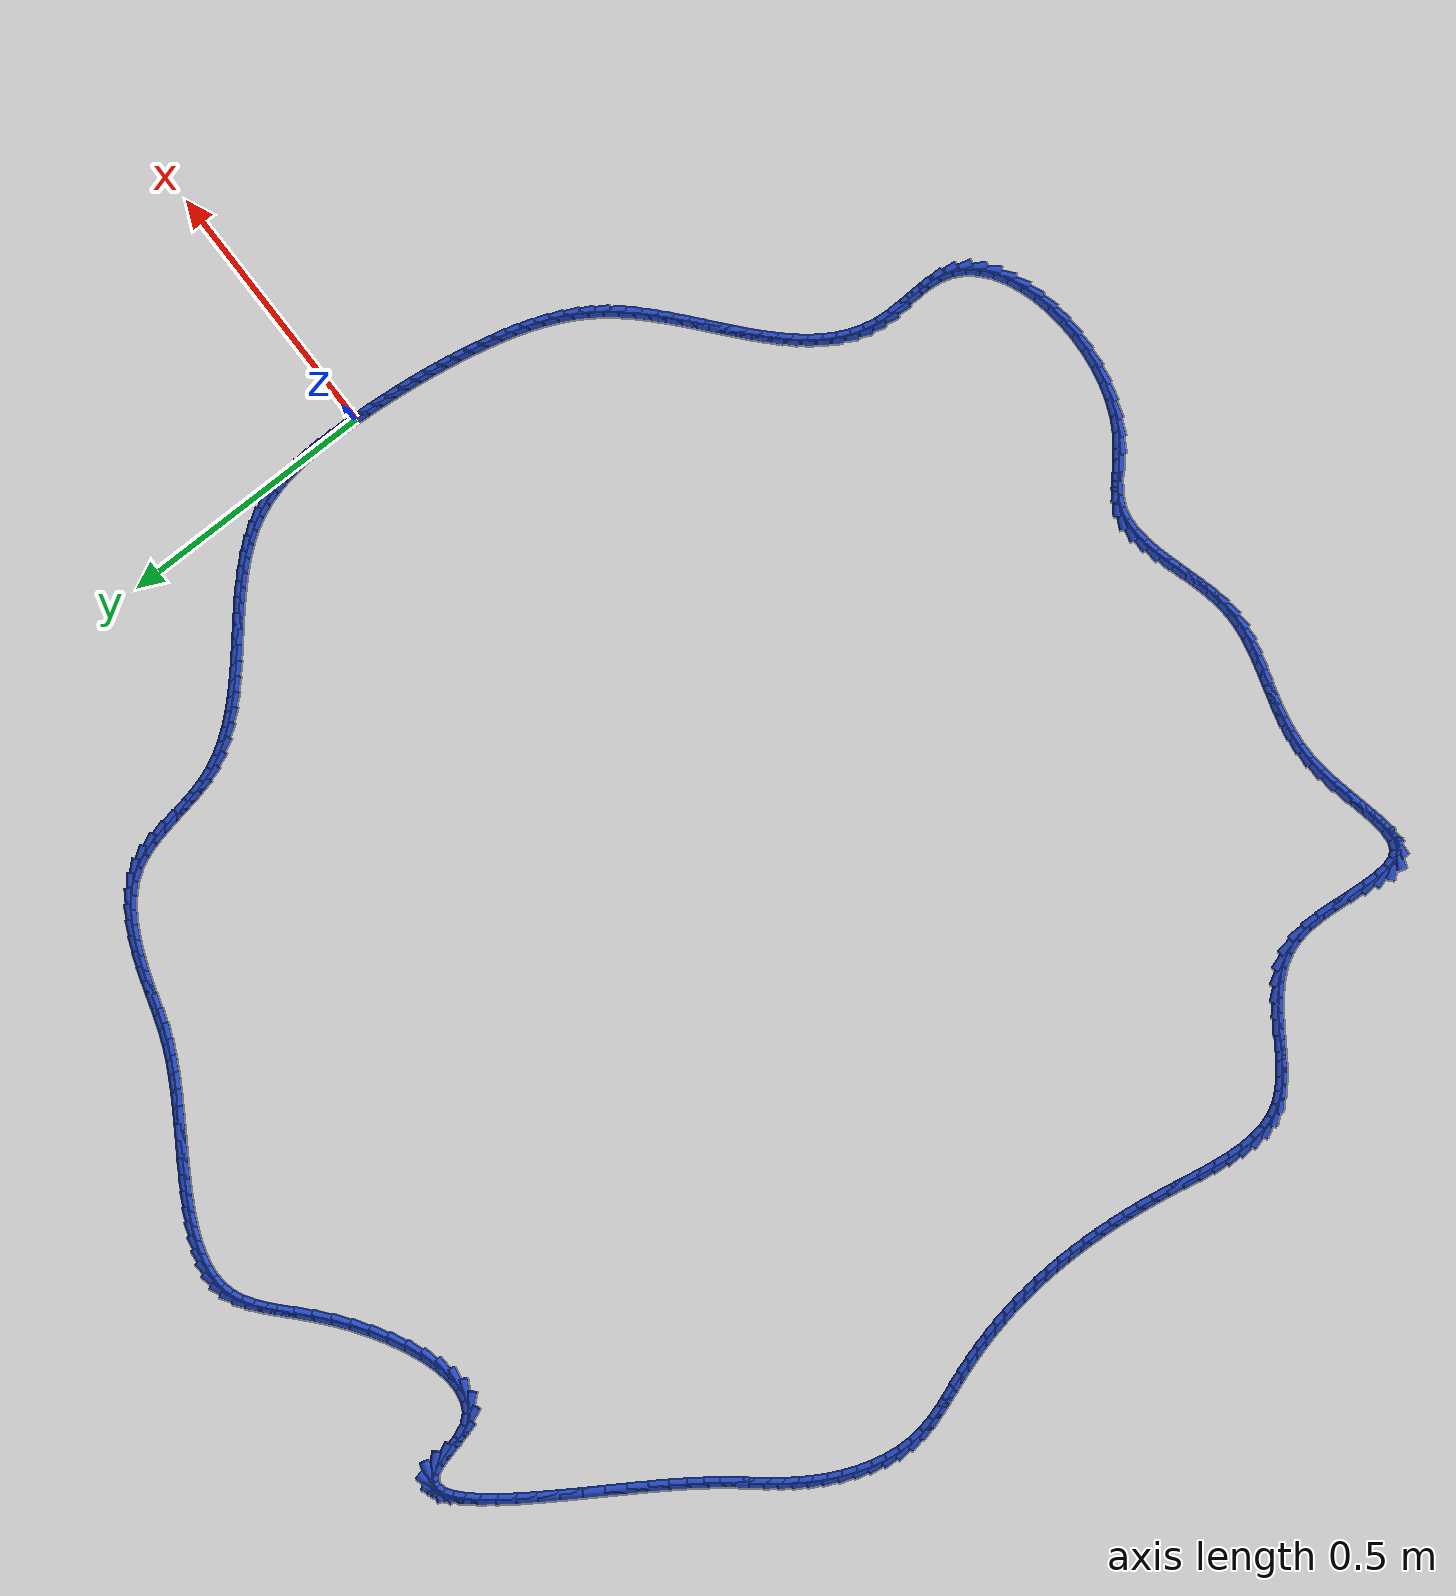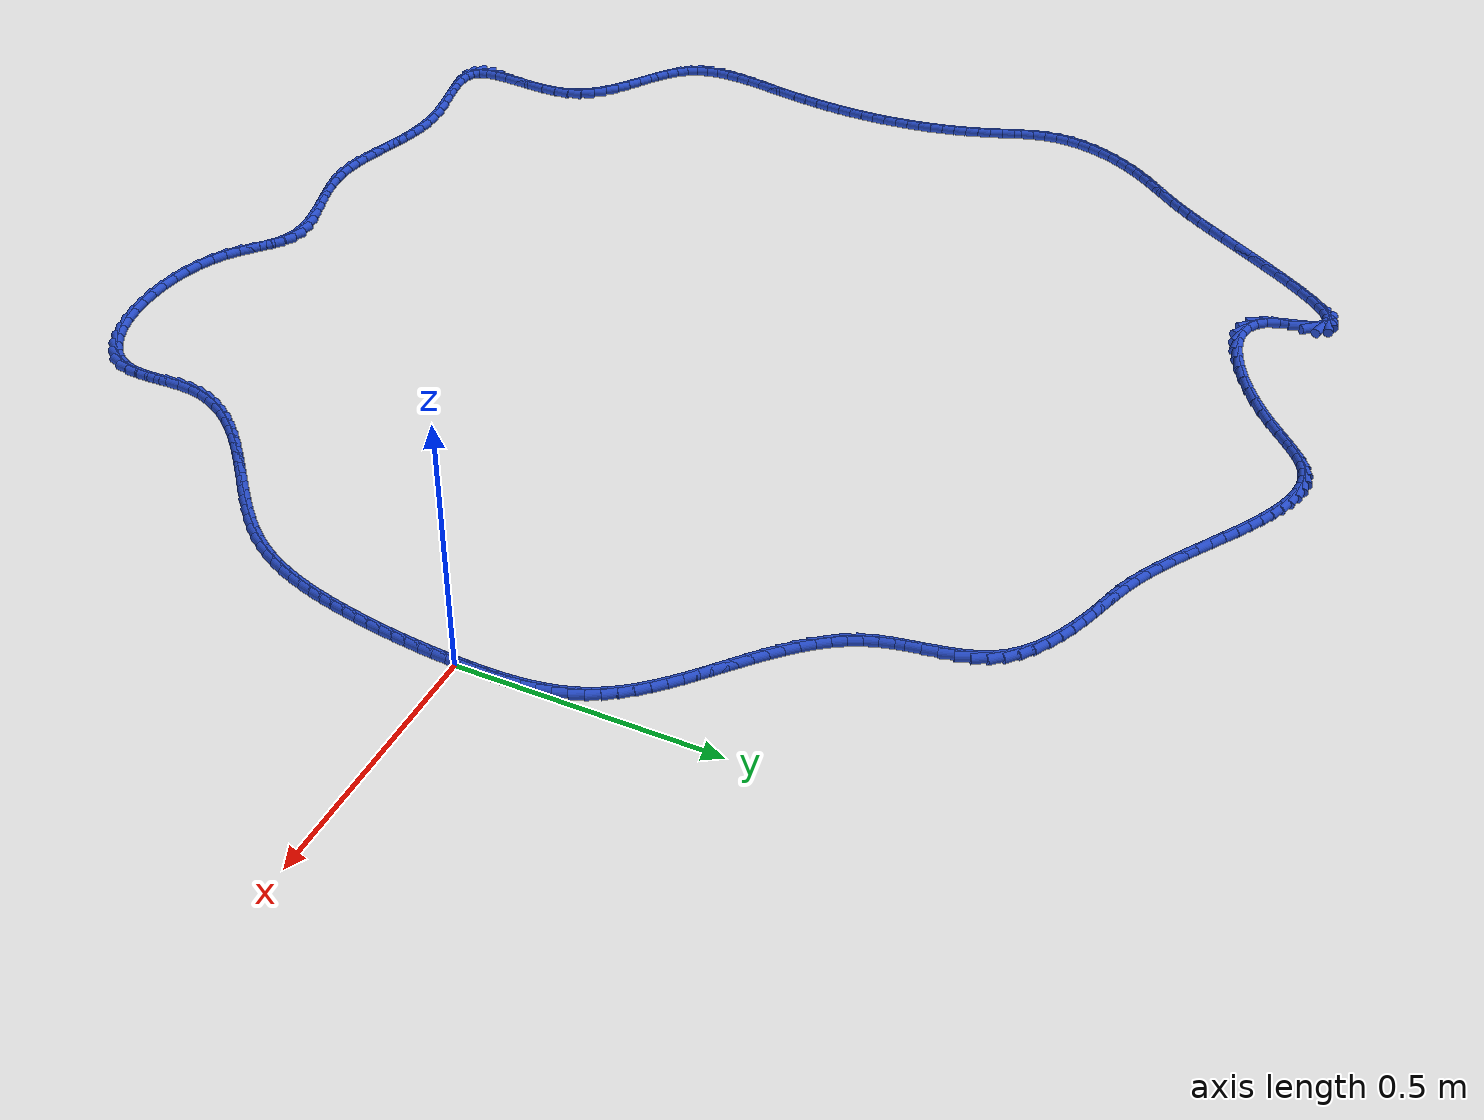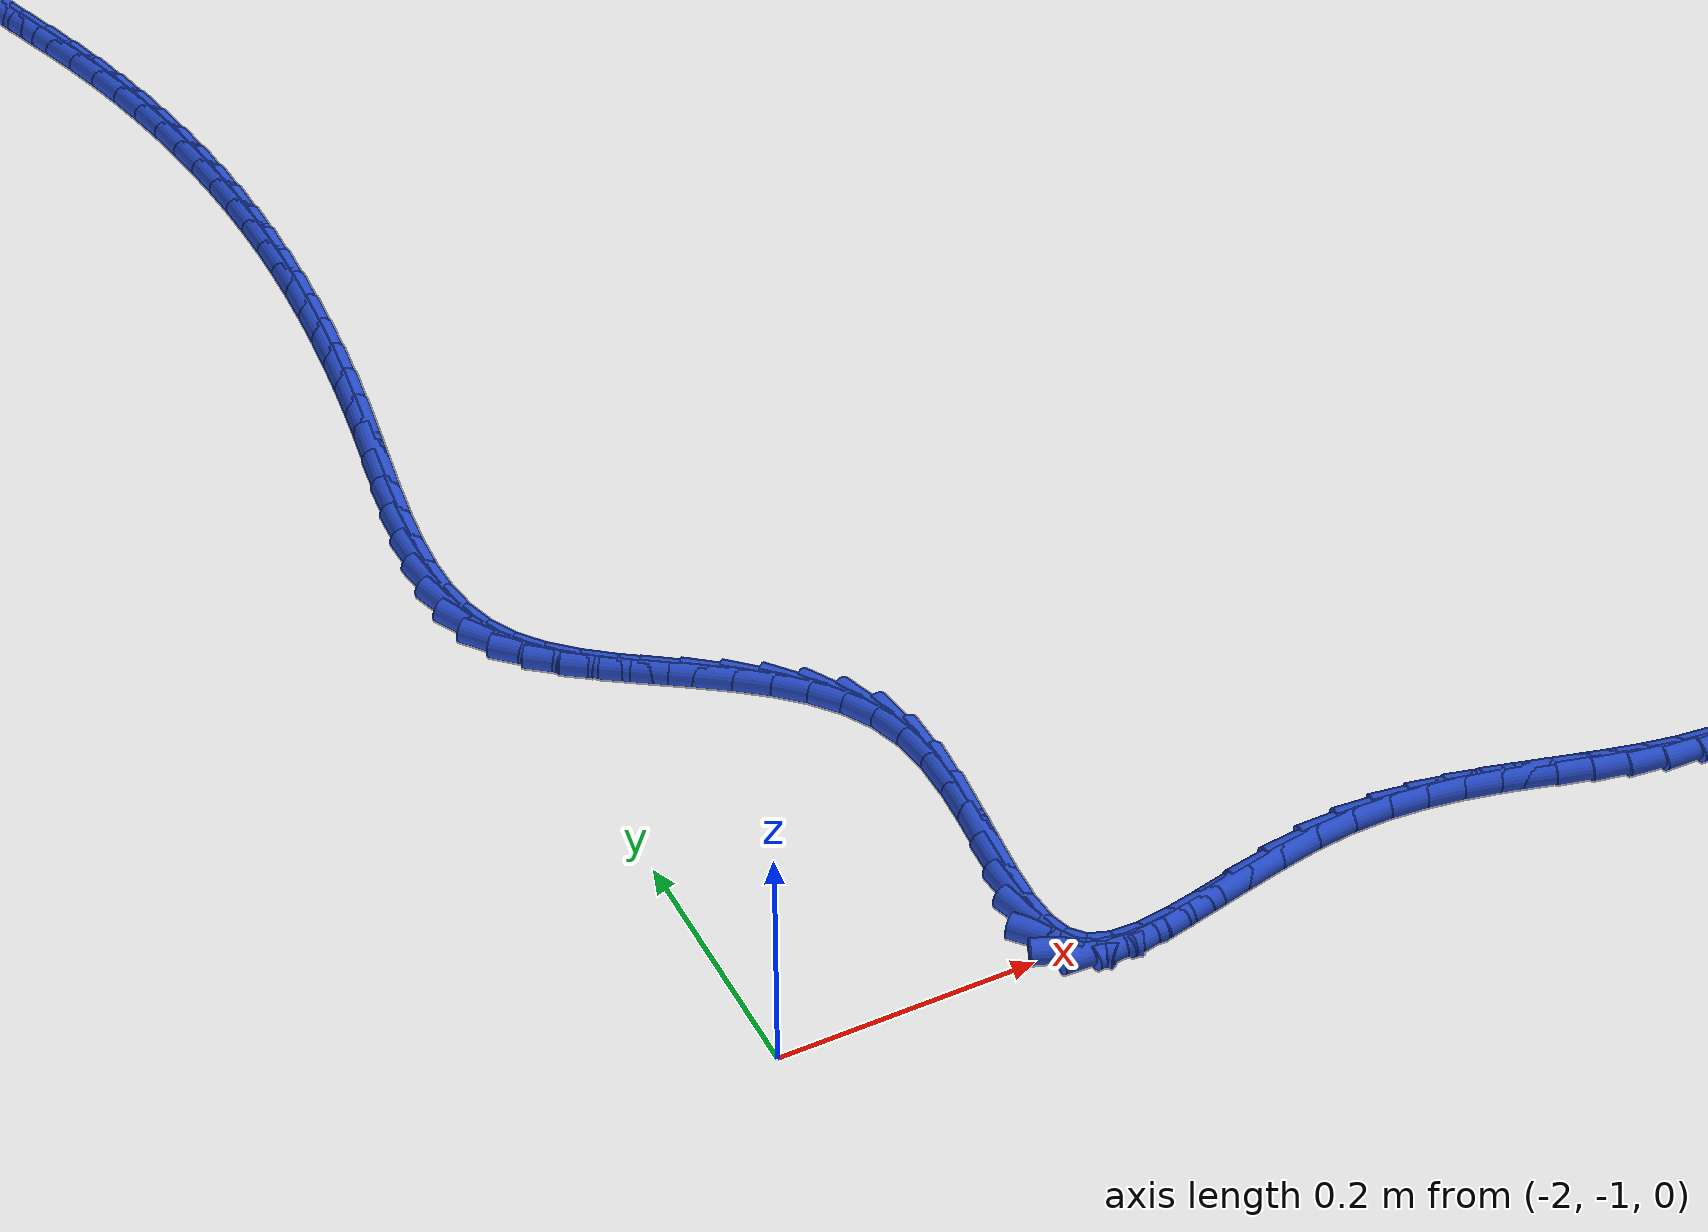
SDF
<sdf version="1.6">
 <world name="default">
  <light name="sun" type="directional">
   <pose>0 0 10 0 -0 0</pose>
   <diffuse>0.8 0.8 0.8 1</diffuse>
   <specular>0.2 0.2 0.2 1</specular>
   <attenuation>
    <range>1000</range>
    <constant>0.9</constant>
    <linear>0.01</linear>
    <quadratic>0.001</quadratic>
   </attenuation>
   <direction>-0.5 0.1 -0.9</direction>
  </light>
  <model name="ground_plane">
   <static>1</static>
   <link name="link">
    <collision name="collision">
     <geometry><plane><normal>0 0 1</normal><size>100 100</size></plane></geometry>
     <surface><friction><ode><mu>100</mu><mu2>50</mu2></ode></friction></surface>
    </collision>
    <visual name="visual">
     <cast_shadows>0</cast_shadows>
     <geometry><plane><normal>0 0 1</normal><size>100 100</size></plane></geometry>
     <material>
      <script><uri>file://media/materials/scripts/gazebo.material</uri><name>Gazebo/WhiteGlow</name></script>
     </material>
    </visual>
   </link>
  </model>
  <gravity>0 0 -9.8</gravity>
  <magnetic_field>6e-06 2.3e-05 -4.2e-05</magnetic_field>
  <atmosphere type="adiabatic"/>
  <physics name="default_physics" default="0" type="ode">
   <max_step_size>0.001</max_step_size>
   <real_time_factor>1</real_time_factor>
   <real_time_update_rate>1000</real_time_update_rate>
  </physics>
  <scene><ambient>0.4 0.4 0.4 1</ambient><background>0.7 0.7 0.7 1</background><shadows>1</shadows></scene>
  <spherical_coordinates>
   <surface_model>EARTH_WGS84</surface_model>
   <latitude_deg>0</latitude_deg>
   <longitude_deg>0</longitude_deg>
   <elevation>0</elevation>
   <heading_deg>0</heading_deg>
  </spherical_coordinates>
  <model name="line">
   <link name="link_0">
    <pose>2.0599841277224584e-18 -3.469446951953614e-17 0.01 0 1.57 1.5281487675419672</pose>
    <collision name="collision">
     <geometry><cylinder><radius>0.01</radius><length>0.08</length></cylinder></geometry>
    </collision>
    <visual name="visual">
     <material>
      <script><name>Gazebo/Blue</name><uri>file://media/materials/scripts/gazebo.material</uri></script>
     </material>
     <geometry><cylinder><radius>0.01</radius><length>0.08</length></cylinder></geometry>
    </visual>
   </link>
   <link name="link_1">
    <pose>0.0012043785383627386 0.028223145487989088 0.01 0 1.57 1.5499418370346412</pose>
    <collision name="collision">
     <geometry><cylinder><radius>0.01</radius><length>0.08</length></cylinder></geometry>
    </collision>
    <visual name="visual">
     <material>
      <script><name>Gazebo/Blue</name><uri>file://media/materials/scripts/gazebo.material</uri></script>
     </material>
     <geometry><cylinder><radius>0.01</radius><length>0.08</length></cylinder></geometry>
    </visual>
   </link>
   <link name="link_2">
    <pose>0.0017961622781648974 0.056595834212515225 0.01 0 1.57 -1.5616119427103334</pose>
    <collision name="collision">
     <geometry><cylinder><radius>0.01</radius><length>0.08</length></cylinder></geometry>
    </collision>
    <visual name="visual">
     <material>
      <script><name>Gazebo/Blue</name><uri>file://media/materials/scripts/gazebo.material</uri></script>
     </material>
     <geometry><cylinder><radius>0.01</radius><length>0.08</length></cylinder></geometry>
    </visual>
   </link>
   <link name="link_3">
    <pose>0.001535870714194465 0.08493570357654158 0.01 0 1.57 -1.5227670737437309</pose>
    <collision name="collision">
     <geometry><cylinder><radius>0.01</radius><length>0.08</length></cylinder></geometry>
    </collision>
    <visual name="visual">
     <material>
      <script><name>Gazebo/Blue</name><uri>file://media/materials/scripts/gazebo.material</uri></script>
     </material>
     <geometry><cylinder><radius>0.01</radius><length>0.08</length></cylinder></geometry>
    </visual>
   </link>
   <link name="link_4">
    <pose>0.00018402334123942925 0.11306039098303124 0.01 0 1.57 -1.4743364225109419</pose>
    <collision name="collision">
     <geometry><cylinder><radius>0.01</radius><length>0.08</length></cylinder></geometry>
    </collision>
    <visual name="visual">
     <material>
      <script><name>Gazebo/Blue</name><uri>file://media/materials/scripts/gazebo.material</uri></script>
     </material>
     <geometry><cylinder><radius>0.01</radius><length>0.08</length></cylinder></geometry>
    </visual>
   </link>
   <link name="link_5">
    <pose>-0.0024988603459122224 0.14078753383494746 0.01 0 1.57 -1.4153808807474224</pose>
    <collision name="collision">
     <geometry><cylinder><radius>0.01</radius><length>0.08</length></cylinder></geometry>
    </collision>
    <visual name="visual">
     <material>
      <script><name>Gazebo/Blue</name><uri>file://media/materials/scripts/gazebo.material</uri></script>
     </material>
     <geometry><cylinder><radius>0.01</radius><length>0.08</length></cylinder></geometry>
    </visual>
   </link>
   <link name="link_6">
    <pose>-0.006752260852472505 0.16793476953525333 0.01 0 1.57 -1.3449131231583356</pose>
    <collision name="collision">
     <geometry><cylinder><radius>0.01</radius><length>0.08</length></cylinder></geometry>
    </collision>
    <visual name="visual">
     <material>
      <script><name>Gazebo/Blue</name><uri>file://media/materials/scripts/gazebo.material</uri></script>
     </material>
     <geometry><cylinder><radius>0.01</radius><length>0.08</length></cylinder></geometry>
    </visual>
   </link>
   <link name="link_7">
    <pose>-0.012815658683653426 0.194319735486912 0.01 0 1.57 -1.2620931907068431</pose>
    <collision name="collision">
     <geometry><cylinder><radius>0.01</radius><length>0.08</length></cylinder></geometry>
    </collision>
    <visual name="visual">
     <material>
      <script><name>Gazebo/Blue</name><uri>file://media/materials/scripts/gazebo.material</uri></script>
     </material>
     <geometry><cylinder><radius>0.01</radius><length>0.08</length></cylinder></geometry>
    </visual>
   </link>
   <link name="link_8">
    <pose>-0.020928534344667002 0.2197600690928867 0.01 0 1.57 -1.1665671507916342</pose>
    <collision name="collision">
     <geometry><cylinder><radius>0.01</radius><length>0.08</length></cylinder></geometry>
    </collision>
    <visual name="visual">
     <material>
      <script><name>Gazebo/Blue</name><uri>file://media/materials/scripts/gazebo.material</uri></script>
     </material>
     <geometry><cylinder><radius>0.01</radius><length>0.08</length></cylinder></geometry>
    </visual>
   </link>
   <link name="link_9">
    <pose>-0.031329664178705995 0.24407385525869985 0.01 0 1.57 -1.0655260045382065</pose>
    <collision name="collision">
     <geometry><cylinder><radius>0.01</radius><length>0.08</length></cylinder></geometry>
    </collision>
    <visual name="visual">
     <material>
      <script><name>Gazebo/Blue</name><uri>file://media/materials/scripts/gazebo.material</uri></script>
     </material>
     <geometry><cylinder><radius>0.01</radius><length>0.08</length></cylinder></geometry>
    </visual>
   </link>
   <link name="link_10">
    <pose>-0.044108063827259646 0.26717435343132306 0.01 0 1.57 -0.975439242324673</pose>
    <collision name="collision">
     <geometry><cylinder><radius>0.01</radius><length>0.08</length></cylinder></geometry>
    </collision>
    <visual name="visual">
     <material>
      <script><name>Gazebo/Blue</name><uri>file://media/materials/scripts/gazebo.material</uri></script>
     </material>
     <geometry><cylinder><radius>0.01</radius><length>0.08</length></cylinder></geometry>
    </visual>
   </link>
   <link name="link_11">
    <pose>-0.05901837780581074 0.28918731951527366 0.01 0 1.57 -0.899314491709051</pose>
    <collision name="collision">
     <geometry><cylinder><radius>0.01</radius><length>0.08</length></cylinder></geometry>
    </collision>
    <visual name="visual">
     <material>
      <script><name>Gazebo/Blue</name><uri>file://media/materials/scripts/gazebo.material</uri></script>
     </material>
     <geometry><cylinder><radius>0.01</radius><length>0.08</length></cylinder></geometry>
    </visual>
   </link>
   <link name="link_12">
    <pose>-0.07576997154769693 0.31026728476021237 0.01 0 1.57 -0.8371411409186568</pose>
    <collision name="collision">
     <geometry><cylinder><radius>0.01</radius><length>0.08</length></cylinder></geometry>
    </collision>
    <visual name="visual">
     <material>
      <script><name>Gazebo/Blue</name><uri>file://media/materials/scripts/gazebo.material</uri></script>
     </material>
     <geometry><cylinder><radius>0.01</radius><length>0.08</length></cylinder></geometry>
    </visual>
   </link>
   <link name="link_13">
    <pose>-0.09407221048625582 0.33056878041579957 0.01 0 1.57 -0.7883366950720202</pose>
    <collision name="collision">
     <geometry><cylinder><radius>0.01</radius><length>0.08</length></cylinder></geometry>
    </collision>
    <visual name="visual">
     <material>
      <script><name>Gazebo/Blue</name><uri>file://media/materials/scripts/gazebo.material</uri></script>
     </material>
     <geometry><cylinder><radius>0.01</radius><length>0.08</length></cylinder></geometry>
    </visual>
   </link>
   <link name="link_14">
    <pose>-0.11363446005482505 0.350246337731696 0.01 0 1.57 -0.7521069230096045</pose>
    <collision name="collision">
     <geometry><cylinder><radius>0.01</radius><length>0.08</length></cylinder></geometry>
    </collision>
    <visual name="visual">
     <material>
      <script><name>Gazebo/Blue</name><uri>file://media/materials/scripts/gazebo.material</uri></script>
     </material>
     <geometry><cylinder><radius>0.01</radius><length>0.08</length></cylinder></geometry>
    </visual>
   </link>
   <link name="link_15">
    <pose>-0.1341660856867423 0.369454487957562 0.01 0 1.57 -0.7276847124320796</pose>
    <collision name="collision">
     <geometry><cylinder><radius>0.01</radius><length>0.08</length></cylinder></geometry>
    </collision>
    <visual name="visual">
     <material>
      <script><name>Gazebo/Blue</name><uri>file://media/materials/scripts/gazebo.material</uri></script>
     </material>
     <geometry><cylinder><radius>0.01</radius><length>0.08</length></cylinder></geometry>
    </visual>
   </link>
   <link name="link_16">
    <pose>-0.15537645281534512 0.3883477623430582 0.01 0 1.57 -0.714467407319368</pose>
    <collision name="collision">
     <geometry><cylinder><radius>0.01</radius><length>0.08</length></cylinder></geometry>
    </collision>
    <visual name="visual">
     <material>
      <script><name>Gazebo/Blue</name><uri>file://media/materials/scripts/gazebo.material</uri></script>
     </material>
     <geometry><cylinder><radius>0.01</radius><length>0.08</length></cylinder></geometry>
    </visual>
   </link>
   <link name="link_17">
    <pose>-0.17697492687397123 0.4070806921378452 0.01 0 1.57 -0.7120858264526755</pose>
    <collision name="collision">
     <geometry><cylinder><radius>0.01</radius><length>0.08</length></cylinder></geometry>
    </collision>
    <visual name="visual">
     <material>
      <script><name>Gazebo/Blue</name><uri>file://media/materials/scripts/gazebo.material</uri></script>
     </material>
     <geometry><cylinder><radius>0.01</radius><length>0.08</length></cylinder></geometry>
    </visual>
   </link>
   <link name="link_18">
    <pose>-0.19867087329595826 0.4258078085915834 0.01 0 1.57 -0.7204317749395995</pose>
    <collision name="collision">
     <geometry><cylinder><radius>0.01</radius><length>0.08</length></cylinder></geometry>
    </collision>
    <visual name="visual">
     <material>
      <script><name>Gazebo/Blue</name><uri>file://media/materials/scripts/gazebo.material</uri></script>
     </material>
     <geometry><cylinder><radius>0.01</radius><length>0.08</length></cylinder></geometry>
    </visual>
   </link>
   <link name="link_19">
    <pose>-0.22017365751464374 0.4446836429539336 0.01 0 1.57 -0.7396591355670677</pose>
    <collision name="collision">
     <geometry><cylinder><radius>0.01</radius><length>0.08</length></cylinder></geometry>
    </collision>
    <visual name="visual">
     <material>
      <script><name>Gazebo/Blue</name><uri>file://media/materials/scripts/gazebo.material</uri></script>
     </material>
     <geometry><cylinder><radius>0.01</radius><length>0.08</length></cylinder></geometry>
    </visual>
   </link>
   <link name="link_20">
    <pose>-0.24119264496336543 0.46386272647455606 0.01 0 1.57 -0.7701618664448675</pose>
    <collision name="collision">
     <geometry><cylinder><radius>0.01</radius><length>0.08</length></cylinder></geometry>
    </collision>
    <visual name="visual">
     <material>
      <script><name>Gazebo/Blue</name><uri>file://media/materials/scripts/gazebo.material</uri></script>
     </material>
     <geometry><cylinder><radius>0.01</radius><length>0.08</length></cylinder></geometry>
    </visual>
   </link>
   <link name="link_21">
    <pose>-0.2614372010754609 0.4834995904031115 0.01 0 1.57 -0.8125211470441647</pose>
    <collision name="collision">
     <geometry><cylinder><radius>0.01</radius><length>0.08</length></cylinder></geometry>
    </collision>
    <visual name="visual">
     <material>
      <script><name>Gazebo/Blue</name><uri>file://media/materials/scripts/gazebo.material</uri></script>
     </material>
     <geometry><cylinder><radius>0.01</radius><length>0.08</length></cylinder></geometry>
    </visual>
   </link>
   <link name="link_22">
    <pose>-0.28061669128426786 0.5037487659892605 0.01 0 1.57 -0.8674034542908987</pose>
    <collision name="collision">
     <geometry><cylinder><radius>0.01</radius><length>0.08</length></cylinder></geometry>
    </collision>
    <visual name="visual">
     <material>
      <script><name>Gazebo/Blue</name><uri>file://media/materials/scripts/gazebo.material</uri></script>
     </material>
     <geometry><cylinder><radius>0.01</radius><length>0.08</length></cylinder></geometry>
    </visual>
   </link>
   <link name="link_23">
    <pose>-0.2984404810231238 0.5247647844826637 0.01 0 1.57 -0.9353838550116299</pose>
    <collision name="collision">
     <geometry><cylinder><radius>0.01</radius><length>0.08</length></cylinder></geometry>
    </collision>
    <visual name="visual">
     <material>
      <script><name>Gazebo/Blue</name><uri>file://media/materials/scripts/gazebo.material</uri></script>
     </material>
     <geometry><cylinder><radius>0.01</radius><length>0.08</length></cylinder></geometry>
    </visual>
   </link>
   <link name="link_24">
    <pose>-0.31461793572536656 0.5467021771329813 0.01 0 1.57 -1.0166723833138167</pose>
    <collision name="collision">
     <geometry><cylinder><radius>0.01</radius><length>0.08</length></cylinder></geometry>
    </collision>
    <visual name="visual">
     <material>
      <script><name>Gazebo/Blue</name><uri>file://media/materials/scripts/gazebo.material</uri></script>
     </material>
     <geometry><cylinder><radius>0.01</radius><length>0.08</length></cylinder></geometry>
    </visual>
   </link>
   <link name="link_25">
    <pose>-0.3288584208243336 0.5697154751898742 0.01 0 1.57 -1.1107515384500188</pose>
    <collision name="collision">
     <geometry><cylinder><radius>0.01</radius><length>0.08</length></cylinder></geometry>
    </collision>
    <visual name="visual">
     <material>
      <script><name>Gazebo/Blue</name><uri>file://media/materials/scripts/gazebo.material</uri></script>
     </material>
     <geometry><cylinder><radius>0.01</radius><length>0.08</length></cylinder></geometry>
    </visual>
   </link>
   <link name="link_26">
    <pose>-0.34087130175336267 0.593959209903003 0.01 0 1.57 -1.2155780729853922</pose>
    <collision name="collision">
     <geometry><cylinder><radius>0.01</radius><length>0.08</length></cylinder></geometry>
    </collision>
    <visual name="visual">
     <material>
      <script><name>Gazebo/Blue</name><uri>file://media/materials/scripts/gazebo.material</uri></script>
     </material>
     <geometry><cylinder><radius>0.01</radius><length>0.08</length></cylinder></geometry>
    </visual>
   </link>
   <link name="link_27">
    <pose>-0.350376151693079 0.619581969996678 0.01 0 1.57 -1.309947642911225</pose>
    <collision name="collision">
     <geometry><cylinder><radius>0.01</radius><length>0.08</length></cylinder></geometry>
    </collision>
    <visual name="visual">
     <material>
      <script><name>Gazebo/Blue</name><uri>file://media/materials/scripts/gazebo.material</uri></script>
     </material>
     <geometry><cylinder><radius>0.01</radius><length>0.08</length></cylinder></geometry>
    </visual>
   </link>
   <link name="link_28">
    <pose>-0.3575520145590481 0.6464648594688834 0.01 0 1.57 -1.3688499180485438</pose>
    <collision name="collision">
     <geometry><cylinder><radius>0.01</radius><length>0.08</length></cylinder></geometry>
    </collision>
    <visual name="visual">
     <material>
      <script><name>Gazebo/Blue</name><uri>file://media/materials/scripts/gazebo.material</uri></script>
     </material>
     <geometry><cylinder><radius>0.01</radius><length>0.08</length></cylinder></geometry>
    </visual>
   </link>
   <link name="link_29">
    <pose>-0.36321380648351437 0.674118803995187 0.01 0 1.57 -1.393199049766554</pose>
    <collision name="collision">
     <geometry><cylinder><radius>0.01</radius><length>0.08</length></cylinder></geometry>
    </collision>
    <visual name="visual">
     <material>
      <script><name>Gazebo/Blue</name><uri>file://media/materials/scripts/gazebo.material</uri></script>
     </material>
     <geometry><cylinder><radius>0.01</radius><length>0.08</length></cylinder></geometry>
    </visual>
   </link>
   <link name="link_30">
    <pose>-0.3682231034023978 0.7020275658566973 0.01 0 1.57 -1.3842431241705004</pose>
    <collision name="collision">
     <geometry><cylinder><radius>0.01</radius><length>0.08</length></cylinder></geometry>
    </collision>
    <visual name="visual">
     <material>
      <script><name>Gazebo/Blue</name><uri>file://media/materials/scripts/gazebo.material</uri></script>
     </material>
     <geometry><cylinder><radius>0.01</radius><length>0.08</length></cylinder></geometry>
    </visual>
   </link>
   <link name="link_31">
    <pose>-0.37344148125161736 0.7296749073345218 0.01 0 1.57 -1.3408782997451967</pose>
    <collision name="collision">
     <geometry><cylinder><radius>0.01</radius><length>0.08</length></cylinder></geometry>
    </collision>
    <visual name="visual">
     <material>
      <script><name>Gazebo/Blue</name><uri>file://media/materials/scripts/gazebo.material</uri></script>
     </material>
     <geometry><cylinder><radius>0.01</radius><length>0.08</length></cylinder></geometry>
    </visual>
   </link>
   <link name="link_32">
    <pose>-0.3797305159670934 0.7565445907097692 0.01 0 1.57 -1.2597810834226935</pose>
    <collision name="collision">
     <geometry><cylinder><radius>0.01</radius><length>0.08</length></cylinder></geometry>
    </collision>
    <visual name="visual">
     <material>
      <script><name>Gazebo/Blue</name><uri>file://media/materials/scripts/gazebo.material</uri></script>
     </material>
     <geometry><cylinder><radius>0.01</radius><length>0.08</length></cylinder></geometry>
    </visual>
   </link>
   <link name="link_33">
    <pose>-0.38795178348474474 0.7821203782635461 0.01 0 1.57 -1.1367832281377155</pose>
    <collision name="collision">
     <geometry><cylinder><radius>0.01</radius><length>0.08</length></cylinder></geometry>
    </collision>
    <visual name="visual">
     <material>
      <script><name>Gazebo/Blue</name><uri>file://media/materials/scripts/gazebo.material</uri></script>
     </material>
     <geometry><cylinder><radius>0.01</radius><length>0.08</length></cylinder></geometry>
    </visual>
   </link>
   <link name="link_34">
    <pose>-0.3989668597404914 0.8058860322769613 0.01 0 1.57 -0.973807297113083</pose>
    <collision name="collision">
     <geometry><cylinder><radius>0.01</radius><length>0.08</length></cylinder></geometry>
    </collision>
    <visual name="visual">
     <material>
      <script><name>Gazebo/Blue</name><uri>file://media/materials/scripts/gazebo.material</uri></script>
     </material>
     <geometry><cylinder><radius>0.01</radius><length>0.08</length></cylinder></geometry>
    </visual>
   </link>
   <link name="link_35">
    <pose>-0.41356458634066595 0.8273619419473335 0.01 0 1.57 -0.8120310284484058</pose>
    <collision name="collision">
     <geometry><cylinder><radius>0.01</radius><length>0.08</length></cylinder></geometry>
    </collision>
    <visual name="visual">
     <material>
      <script><name>Gazebo/Blue</name><uri>file://media/materials/scripts/gazebo.material</uri></script>
     </material>
     <geometry><cylinder><radius>0.01</radius><length>0.08</length></cylinder></geometry>
    </visual>
   </link>
   <link name="link_36">
    <pose>-0.43169894286518734 0.8464889089740674 0.01 0 1.57 -0.6780404586303507</pose>
    <collision name="collision">
     <geometry><cylinder><radius>0.01</radius><length>0.08</length></cylinder></geometry>
    </collision>
    <visual name="visual">
     <material>
      <script><name>Gazebo/Blue</name><uri>file://media/materials/scripts/gazebo.material</uri></script>
     </material>
     <geometry><cylinder><radius>0.01</radius><length>0.08</length></cylinder></geometry>
    </visual>
   </link>
   <link name="link_37">
    <pose>-0.4527903139765916 0.863476438108354 0.01 0 1.57 -0.5707481826740988</pose>
    <collision name="collision">
     <geometry><cylinder><radius>0.01</radius><length>0.08</length></cylinder></geometry>
    </collision>
    <visual name="visual">
     <material>
      <script><name>Gazebo/Blue</name><uri>file://media/materials/scripts/gazebo.material</uri></script>
     </material>
     <geometry><cylinder><radius>0.01</radius><length>0.08</length></cylinder></geometry>
    </visual>
   </link>
   <link name="link_38">
    <pose>-0.47625041418115344 0.8785384001426848 0.01 0 1.57 -0.48651620027274195</pose>
    <collision name="collision">
     <geometry><cylinder><radius>0.01</radius><length>0.08</length></cylinder></geometry>
    </collision>
    <visual name="visual">
     <material>
      <script><name>Gazebo/Blue</name><uri>file://media/materials/scripts/gazebo.material</uri></script>
     </material>
     <geometry><cylinder><radius>0.01</radius><length>0.08</length></cylinder></geometry>
    </visual>
   </link>
   <link name="link_39">
    <pose>-0.5014909579851474 0.8918886658695505 0.01 0 1.57 -0.4215230936939067</pose>
    <collision name="collision">
     <geometry><cylinder><radius>0.01</radius><length>0.08</length></cylinder></geometry>
    </collision>
    <visual name="visual">
     <material>
      <script><name>Gazebo/Blue</name><uri>file://media/materials/scripts/gazebo.material</uri></script>
     </material>
     <geometry><cylinder><radius>0.01</radius><length>0.08</length></cylinder></geometry>
    </visual>
   </link>
   <link name="link_40">
    <pose>-0.5279236598948476 0.9037411060814424 0.01 0 1.57 -0.37263344083006067</pose>
    <collision name="collision">
     <geometry><cylinder><radius>0.01</radius><length>0.08</length></cylinder></geometry>
    </collision>
    <visual name="visual">
     <material>
      <script><name>Gazebo/Blue</name><uri>file://media/materials/scripts/gazebo.material</uri></script>
     </material>
     <geometry><cylinder><radius>0.01</radius><length>0.08</length></cylinder></geometry>
    </visual>
   </link>
   <link name="link_41">
    <pose>-0.5549602344165292 0.9143095915708516 0.01 0 1.57 -0.33766719422047237</pose>
    <collision name="collision">
     <geometry><cylinder><radius>0.01</radius><length>0.08</length></cylinder></geometry>
    </collision>
    <visual name="visual">
     <material>
      <script><name>Gazebo/Blue</name><uri>file://media/materials/scripts/gazebo.material</uri></script>
     </material>
     <geometry><cylinder><radius>0.01</radius><length>0.08</length></cylinder></geometry>
    </visual>
   </link>
   <link name="link_42">
    <pose>-0.5820123960564667 0.9238079931302692 0.01 0 1.57 -0.3158640826543507</pose>
    <collision name="collision">
     <geometry><cylinder><radius>0.01</radius><length>0.08</length></cylinder></geometry>
    </collision>
    <visual name="visual">
     <material>
      <script><name>Gazebo/Blue</name><uri>file://media/materials/scripts/gazebo.material</uri></script>
     </material>
     <geometry><cylinder><radius>0.01</radius><length>0.08</length></cylinder></geometry>
    </visual>
   </link>
   <link name="link_43">
    <pose>-0.6085230810983535 0.9324718319329308 0.01 0 1.57 -0.3138710922903581</pose>
    <collision name="collision">
     <geometry><cylinder><radius>0.01</radius><length>0.08</length></cylinder></geometry>
    </collision>
    <visual name="visual">
     <material>
      <script><name>Gazebo/Blue</name><uri>file://media/materials/scripts/gazebo.material</uri></script>
     </material>
     <geometry><cylinder><radius>0.01</radius><length>0.08</length></cylinder></geometry>
    </visual>
   </link>
   <link name="link_44">
    <pose>-0.6344341278122992 0.9408825869691143 0.01 0 1.57 -0.33800140475630647</pose>
    <collision name="collision">
     <geometry><cylinder><radius>0.01</radius><length>0.08</length></cylinder></geometry>
    </collision>
    <visual name="visual">
     <material>
      <script><name>Gazebo/Blue</name><uri>file://media/materials/scripts/gazebo.material</uri></script>
     </material>
     <geometry><cylinder><radius>0.01</radius><length>0.08</length></cylinder></geometry>
    </visual>
   </link>
   <link name="link_45">
    <pose>-0.6600883351554628 0.9498997787839286 0.01 0 1.57 -0.38675559189832476</pose>
    <collision name="collision">
     <geometry><cylinder><radius>0.01</radius><length>0.08</length></cylinder></geometry>
    </collision>
    <visual name="visual">
     <material>
      <script><name>Gazebo/Blue</name><uri>file://media/materials/scripts/gazebo.material</uri></script>
     </material>
     <geometry><cylinder><radius>0.01</radius><length>0.08</length></cylinder></geometry>
    </visual>
   </link>
   <link name="link_46">
    <pose>-0.6858385150947921 0.9603869863259074 0.01 0 1.57 -0.4447675113696836</pose>
    <collision name="collision">
     <geometry><cylinder><radius>0.01</radius><length>0.08</length></cylinder></geometry>
    </collision>
    <visual name="visual">
     <material>
      <script><name>Gazebo/Blue</name><uri>file://media/materials/scripts/gazebo.material</uri></script>
     </material>
     <geometry><cylinder><radius>0.01</radius><length>0.08</length></cylinder></geometry>
    </visual>
   </link>
   <link name="link_47">
    <pose>-0.7118978447260422 0.9728073274264223 0.01 0 1.57 -0.4908819002500221</pose>
    <collision name="collision">
     <geometry><cylinder><radius>0.01</radius><length>0.08</length></cylinder></geometry>
    </collision>
    <visual name="visual">
     <material>
      <script><name>Gazebo/Blue</name><uri>file://media/materials/scripts/gazebo.material</uri></script>
     </material>
     <geometry><cylinder><radius>0.01</radius><length>0.08</length></cylinder></geometry>
    </visual>
   </link>
   <link name="link_48">
    <pose>-0.7382188825498427 0.9868764876109711 0.01 0 1.57 -0.5249608125229787</pose>
    <collision name="collision">
     <geometry><cylinder><radius>0.01</radius><length>0.08</length></cylinder></geometry>
    </collision>
    <visual name="visual">
     <material>
      <script><name>Gazebo/Blue</name><uri>file://media/materials/scripts/gazebo.material</uri></script>
     </material>
     <geometry><cylinder><radius>0.01</radius><length>0.08</length></cylinder></geometry>
    </visual>
   </link>
   <link name="link_49">
    <pose>-0.7647256683309209 1.0022283630587194 0.01 0 1.57 -0.5486260765015953</pose>
    <collision name="collision">
     <geometry><cylinder><radius>0.01</radius><length>0.08</length></cylinder></geometry>
    </collision>
    <visual name="visual">
     <material>
      <script><name>Gazebo/Blue</name><uri>file://media/materials/scripts/gazebo.material</uri></script>
     </material>
     <geometry><cylinder><radius>0.01</radius><length>0.08</length></cylinder></geometry>
    </visual>
   </link>
   <link name="link_50">
    <pose>-0.7913422418340027 1.018496849948832 0.01 0 1.57 -0.5629718374270076</pose>
    <collision name="collision">
     <geometry><cylinder><radius>0.01</radius><length>0.08</length></cylinder></geometry>
    </collision>
    <visual name="visual">
     <material>
      <script><name>Gazebo/Blue</name><uri>file://media/materials/scripts/gazebo.material</uri></script>
     </material>
     <geometry><cylinder><radius>0.01</radius><length>0.08</length></cylinder></geometry>
    </visual>
   </link>
   <link name="link_51">
    <pose>-0.8179926428238149 1.0353158444604746 0.01 0 1.57 -0.5686225255396786</pose>
    <collision name="collision">
     <geometry><cylinder><radius>0.01</radius><length>0.08</length></cylinder></geometry>
    </collision>
    <visual name="visual">
     <material>
      <script><name>Gazebo/Blue</name><uri>file://media/materials/scripts/gazebo.material</uri></script>
     </material>
     <geometry><cylinder><radius>0.01</radius><length>0.08</length></cylinder></geometry>
    </visual>
   </link>
   <link name="link_52">
    <pose>-0.8446009110650834 1.0523192427728119 0.01 0 1.57 -0.5657697860172443</pose>
    <collision name="collision">
     <geometry><cylinder><radius>0.01</radius><length>0.08</length></cylinder></geometry>
    </collision>
    <visual name="visual">
     <material>
      <script><name>Gazebo/Blue</name><uri>file://media/materials/scripts/gazebo.material</uri></script>
     </material>
     <geometry><cylinder><radius>0.01</radius><length>0.08</length></cylinder></geometry>
    </visual>
   </link>
   <link name="link_53">
    <pose>-0.871091086322535 1.069140941065009 0.01 0 1.57 -0.5541794447651126</pose>
    <collision name="collision">
     <geometry><cylinder><radius>0.01</radius><length>0.08</length></cylinder></geometry>
    </collision>
    <visual name="visual">
     <material>
      <script><name>Gazebo/Blue</name><uri>file://media/materials/scripts/gazebo.material</uri></script>
     </material>
     <geometry><cylinder><radius>0.01</radius><length>0.08</length></cylinder></geometry>
    </visual>
   </link>
   <link name="link_54">
    <pose>-0.8973872083608959 1.0854148355162314 0.01 0 1.57 -0.5331647149262077</pose>
    <collision name="collision">
     <geometry><cylinder><radius>0.01</radius><length>0.08</length></cylinder></geometry>
    </collision>
    <visual name="visual">
     <material>
      <script><name>Gazebo/Blue</name><uri>file://media/materials/scripts/gazebo.material</uri></script>
     </material>
     <geometry><cylinder><radius>0.01</radius><length>0.08</length></cylinder></geometry>
    </visual>
   </link>
   <link name="link_55">
    <pose>-0.9234133169448928 1.1007748223056442 0.01 0 1.57 -0.501523838635975</pose>
    <collision name="collision">
     <geometry><cylinder><radius>0.01</radius><length>0.08</length></cylinder></geometry>
    </collision>
    <visual name="visual">
     <material>
      <script><name>Gazebo/Blue</name><uri>file://media/materials/scripts/gazebo.material</uri></script>
     </material>
     <geometry><cylinder><radius>0.01</radius><length>0.08</length></cylinder></geometry>
    </visual>
   </link>
   <link name="link_56">
    <pose>-0.9490934518392516 1.1148547976124121 0.01 0 1.57 -0.45744468080448314</pose>
    <collision name="collision">
     <geometry><cylinder><radius>0.01</radius><length>0.08</length></cylinder></geometry>
    </collision>
    <visual name="visual">
     <material>
      <script><name>Gazebo/Blue</name><uri>file://media/materials/scripts/gazebo.material</uri></script>
     </material>
     <geometry><cylinder><radius>0.01</radius><length>0.08</length></cylinder></geometry>
    </visual>
   </link>
   <link name="link_57">
    <pose>-0.9743516528086994 1.127288657615701 0.01 0 1.57 -0.3983937433669224</pose>
    <collision name="collision">
     <geometry><cylinder><radius>0.01</radius><length>0.08</length></cylinder></geometry>
    </collision>
    <visual name="visual">
     <material>
      <script><name>Gazebo/Blue</name><uri>file://media/materials/scripts/gazebo.material</uri></script>
     </material>
     <geometry><cylinder><radius>0.01</radius><length>0.08</length></cylinder></geometry>
    </visual>
   </link>
   <link name="link_58">
    <pose>-0.9991119596179621 1.1377102984946754 0.01 0 1.57 -0.32104960243753217</pose>
    <collision name="collision">
     <geometry><cylinder><radius>0.01</radius><length>0.08</length></cylinder></geometry>
    </collision>
    <visual name="visual">
     <material>
      <script><name>Gazebo/Blue</name><uri>file://media/materials/scripts/gazebo.material</uri></script>
     </material>
     <geometry><cylinder><radius>0.01</radius><length>0.08</length></cylinder></geometry>
    </visual>
   </link>
   <link name="link_59">
    <pose>-1.023298412031766 1.1457536164285012 0.01 0 1.57 -0.22144172937321024</pose>
    <collision name="collision">
     <geometry><cylinder><radius>0.01</radius><length>0.08</length></cylinder></geometry>
    </collision>
    <visual name="visual">
     <material>
      <script><name>Gazebo/Blue</name><uri>file://media/materials/scripts/gazebo.material</uri></script>
     </material>
     <geometry><cylinder><radius>0.01</radius><length>0.08</length></cylinder></geometry>
    </visual>
   </link>
   <link name="link_60">
    <pose>-1.0468350498148382 1.1510525075963425 0.01 0 1.57 -0.09564232067876792</pose>
    <collision name="collision">
     <geometry><cylinder><radius>0.01</radius><length>0.08</length></cylinder></geometry>
    </collision>
    <visual name="visual">
     <material>
      <script><name>Gazebo/Blue</name><uri>file://media/materials/scripts/gazebo.material</uri></script>
     </material>
     <geometry><cylinder><radius>0.01</radius><length>0.08</length></cylinder></geometry>
    </visual>
   </link>
   <link name="link_61">
    <pose>-1.0696459127319042 1.1532408681773654 0.01 0 1.57 0.05846690367612177</pose>
    <collision name="collision">
     <geometry><cylinder><radius>0.01</radius><length>0.08</length></cylinder></geometry>
    </collision>
    <visual name="visual">
     <material>
      <script><name>Gazebo/Blue</name><uri>file://media/materials/scripts/gazebo.material</uri></script>
     </material>
     <geometry><cylinder><radius>0.01</radius><length>0.08</length></cylinder></geometry>
    </visual>
   </link>
   <link name="link_62">
    <pose>-1.091655040547691 1.1519525943507345 0.01 0 1.57 0.2382042147833684</pose>
    <collision name="collision">
     <geometry><cylinder><radius>0.01</radius><length>0.08</length></cylinder></geometry>
    </collision>
    <visual name="visual">
     <material>
      <script><name>Gazebo/Blue</name><uri>file://media/materials/scripts/gazebo.material</uri></script>
     </material>
     <geometry><cylinder><radius>0.01</radius><length>0.08</length></cylinder></geometry>
    </visual>
   </link>
   <link name="link_63">
    <pose>-1.112786473026925 1.1468215822956151 0.01 0 1.57 0.42569937189154256</pose>
    <collision name="collision">
     <geometry><cylinder><radius>0.01</radius><length>0.08</length></cylinder></geometry>
    </collision>
    <visual name="visual">
     <material>
      <script><name>Gazebo/Blue</name><uri>file://media/materials/scripts/gazebo.material</uri></script>
     </material>
     <geometry><cylinder><radius>0.01</radius><length>0.08</length></cylinder></geometry>
    </visual>
   </link>
   <link name="link_64">
    <pose>-1.133051928414438 1.1376326970161832 0.01 0 1.57 0.5736222615817751</pose>
    <collision name="collision">
     <geometry><cylinder><radius>0.01</radius><length>0.08</length></cylinder></geometry>
    </collision>
    <visual name="visual">
     <material>
      <script><name>Gazebo/Blue</name><uri>file://media/materials/scripts/gazebo.material</uri></script>
     </material>
     <geometry><cylinder><radius>0.01</radius><length>0.08</length></cylinder></geometry>
    </visual>
   </link>
   <link name="link_65">
    <pose>-1.152851858330945 1.1248401424573473 0.01 0 1.57 0.67112102603823</pose>
    <collision name="collision">
     <geometry><cylinder><radius>0.01</radius><length>0.08</length></cylinder></geometry>
    </collision>
    <visual name="visual">
     <material>
      <script><name>Gazebo/Blue</name><uri>file://media/materials/scripts/gazebo.material</uri></script>
     </material>
     <geometry><cylinder><radius>0.01</radius><length>0.08</length></cylinder></geometry>
    </visual>
   </link>
   <link name="link_66">
    <pose>-1.172694410885196 1.10908355931243 0.01 0 1.57 0.7253688649471478</pose>
    <collision name="collision">
     <geometry><cylinder><radius>0.01</radius><length>0.08</length></cylinder></geometry>
    </collision>
    <visual name="visual">
     <material>
      <script><name>Gazebo/Blue</name><uri>file://media/materials/scripts/gazebo.material</uri></script>
     </material>
     <geometry><cylinder><radius>0.01</radius><length>0.08</length></cylinder></geometry>
    </visual>
   </link>
   <link name="link_67">
    <pose>-1.1930877381090412 1.0910025950297237 0.01 0 1.57 0.7445029814929888</pose>
    <collision name="collision">
     <geometry><cylinder><radius>0.01</radius><length>0.08</length></cylinder></geometry>
    </collision>
    <visual name="visual">
     <material>
      <script><name>Gazebo/Blue</name><uri>file://media/materials/scripts/gazebo.material</uri></script>
     </material>
     <geometry><cylinder><radius>0.01</radius><length>0.08</length></cylinder></geometry>
    </visual>
   </link>
   <link name="link_68">
    <pose>-1.2145399920343296 1.0712368970575228 0.01 0 1.57 0.7350519117442823</pose>
    <collision name="collision">
     <geometry><cylinder><radius>0.01</radius><length>0.08</length></cylinder></geometry>
    </collision>
    <visual name="visual">
     <material>
      <script><name>Gazebo/Blue</name><uri>file://media/materials/scripts/gazebo.material</uri></script>
     </material>
     <geometry><cylinder><radius>0.01</radius><length>0.08</length></cylinder></geometry>
    </visual>
   </link>
   <link name="link_69">
    <pose>-1.2375593246929113 1.0504261128441206 0.01 0 1.57 0.7018471827969643</pose>
    <collision name="collision">
     <geometry><cylinder><radius>0.01</radius><length>0.08</length></cylinder></geometry>
    </collision>
    <visual name="visual">
     <material>
      <script><name>Gazebo/Blue</name><uri>file://media/materials/scripts/gazebo.material</uri></script>
     </material>
     <geometry><cylinder><radius>0.01</radius><length>0.08</length></cylinder></geometry>
    </visual>
   </link>
   <link name="link_70">
    <pose>-1.2626538881166365 1.0292098898378104 0.01 0 1.57 0.6507447884981931</pose>
    <collision name="collision">
     <geometry><cylinder><radius>0.01</radius><length>0.08</length></cylinder></geometry>
    </collision>
    <visual name="visual">
     <material>
      <script><name>Gazebo/Blue</name><uri>file://media/materials/scripts/gazebo.material</uri></script>
     </material>
     <geometry><cylinder><radius>0.01</radius><length>0.08</length></cylinder></geometry>
    </visual>
   </link>
   <link name="link_71">
    <pose>-1.2902090221353073 1.0082299543242181 0.01 0 1.57 0.5960978263858033</pose>
    <collision name="collision">
     <geometry><cylinder><radius>0.01</radius><length>0.08</length></cylinder></geometry>
    </collision>
    <visual name="visual">
     <material>
      <script><name>Gazebo/Blue</name><uri>file://media/materials/scripts/gazebo.material</uri></script>
     </material>
     <geometry><cylinder><radius>0.01</radius><length>0.08</length></cylinder></geometry>
    </visual>
   </link>
   <link name="link_72">
    <pose>-1.3198196460807194 0.9881414120057719 0.01 0 1.57 0.5396582795383098</pose>
    <collision name="collision">
     <geometry><cylinder><radius>0.01</radius><length>0.08</length></cylinder></geometry>
    </collision>
    <visual name="visual">
     <material>
      <script><name>Gazebo/Blue</name><uri>file://media/materials/scripts/gazebo.material</uri></script>
     </material>
     <geometry><cylinder><radius>0.01</radius><length>0.08</length></cylinder></geometry>
    </visual>
   </link>
   <link name="link_73">
    <pose>-1.3507675933902694 0.9696046681775674 0.01 0 1.57 0.4772733635991667</pose>
    <collision name="collision">
     <geometry><cylinder><radius>0.01</radius><length>0.08</length></cylinder></geometry>
    </collision>
    <visual name="visual">
     <material>
      <script><name>Gazebo/Blue</name><uri>file://media/materials/scripts/gazebo.material</uri></script>
     </material>
     <geometry><cylinder><radius>0.01</radius><length>0.08</length></cylinder></geometry>
    </visual>
   </link>
   <link name="link_74">
    <pose>-1.382333916084575 0.9532801413617124 0.01 0 1.57 0.40399387006309345</pose>
    <collision name="collision">
     <geometry><cylinder><radius>0.01</radius><length>0.08</length></cylinder></geometry>
    </collision>
    <visual name="visual">
     <material>
      <script><name>Gazebo/Blue</name><uri>file://media/materials/scripts/gazebo.material</uri></script>
     </material>
     <geometry><cylinder><radius>0.01</radius><length>0.08</length></cylinder></geometry>
    </visual>
   </link>
   <link name="link_75">
    <pose>-1.4137996661842538 0.9398282500803137 0.01 0 1.57 0.31301585151605144</pose>
    <collision name="collision">
     <geometry><cylinder><radius>0.01</radius><length>0.08</length></cylinder></geometry>
    </collision>
    <visual name="visual">
     <material>
      <script><name>Gazebo/Blue</name><uri>file://media/materials/scripts/gazebo.material</uri></script>
     </material>
     <geometry><cylinder><radius>0.01</radius><length>0.08</length></cylinder></geometry>
    </visual>
   </link>
   <link name="link_76">
    <pose>-1.444445895709923 0.9299094128554787 0.01 0 1.57 0.19421611476089998</pose>
    <collision name="collision">
     <geometry><cylinder><radius>0.01</radius><length>0.08</length></cylinder></geometry>
    </collision>
    <visual name="visual">
     <material>
      <script><name>Gazebo/Blue</name><uri>file://media/materials/scripts/gazebo.material</uri></script>
     </material>
     <geometry><cylinder><radius>0.01</radius><length>0.08</length></cylinder></geometry>
    </visual>
   </link>
   <link name="link_77">
    <pose>-1.4735536566822014 0.924184048209315 0.01 0 1.57 0.03244530908625887</pose>
    <collision name="collision">
     <geometry><cylinder><radius>0.01</radius><length>0.08</length></cylinder></geometry>
    </collision>
    <visual name="visual">
     <material>
      <script><name>Gazebo/Blue</name><uri>file://media/materials/scripts/gazebo.material</uri></script>
     </material>
     <geometry><cylinder><radius>0.01</radius><length>0.08</length></cylinder></geometry>
    </visual>
   </link>
   <link name="link_78">
    <pose>-1.5004040011217061 0.9233125746639298 0.01 0 1.57 -0.1920751924655233</pose>
    <collision name="collision">
     <geometry><cylinder><radius>0.01</radius><length>0.08</length></cylinder></geometry>
    </collision>
    <visual name="visual">
     <material>
      <script><name>Gazebo/Blue</name><uri>file://media/materials/scripts/gazebo.material</uri></script>
     </material>
     <geometry><cylinder><radius>0.01</radius><length>0.08</length></cylinder></geometry>
    </visual>
   </link>
   <link name="link_79">
    <pose>-1.5242779810490537 0.9279554107414298 0.01 0 1.57 -0.4921003853158791</pose>
    <collision name="collision">
     <geometry><cylinder><radius>0.01</radius><length>0.08</length></cylinder></geometry>
    </collision>
    <visual name="visual">
     <material>
      <script><name>Gazebo/Blue</name><uri>file://media/materials/scripts/gazebo.material</uri></script>
     </material>
     <geometry><cylinder><radius>0.01</radius><length>0.08</length></cylinder></geometry>
    </visual>
   </link>
   <link name="link_80">
    <pose>-1.5444566484848639 0.9387729749639231 0.01 0 1.57 -0.8418452201998652</pose>
    <collision name="collision">
     <geometry><cylinder><radius>0.01</radius><length>0.08</length></cylinder></geometry>
    </collision>
    <visual name="visual">
     <material>
      <script><name>Gazebo/Blue</name><uri>file://media/materials/scripts/gazebo.material</uri></script>
     </material>
     <geometry><cylinder><radius>0.01</radius><length>0.08</length></cylinder></geometry>
    </visual>
   </link>
   <link name="link_81">
    <pose>-1.560221055449753 0.9564256858535163 0.01 0 1.57 -1.1553070775471048</pose>
    <collision name="collision">
     <geometry><cylinder><radius>0.01</radius><length>0.08</length></cylinder></geometry>
    </collision>
    <visual name="visual">
     <material>
      <script><name>Gazebo/Blue</name><uri>file://media/materials/scripts/gazebo.material</uri></script>
     </material>
     <geometry><cylinder><radius>0.01</radius><length>0.08</length></cylinder></geometry>
    </visual>
   </link>
   <link name="link_82">
    <pose>-1.5711044463587647 0.9810948954071318 0.01 0 1.57 -1.3072496696569134</pose>
    <collision name="collision">
     <geometry><cylinder><radius>0.01</radius><length>0.08</length></cylinder></geometry>
    </collision>
    <visual name="visual">
     <material>
      <script><name>Gazebo/Blue</name><uri>file://media/materials/scripts/gazebo.material</uri></script>
     </material>
     <geometry><cylinder><radius>0.01</radius><length>0.08</length></cylinder></geometry>
    </visual>
   </link>
   <link name="link_83">
    <pose>-1.5786650068933479 1.0091153623157632 0.01 0 1.57 -1.3146788064199935</pose>
    <collision name="collision">
     <geometry><cylinder><radius>0.01</radius><length>0.08</length></cylinder></geometry>
    </collision>
    <visual name="visual">
     <material>
      <script><name>Gazebo/Blue</name><uri>file://media/materials/scripts/gazebo.material</uri></script>
     </material>
     <geometry><cylinder><radius>0.01</radius><length>0.08</length></cylinder></geometry>
    </visual>
   </link>
   <link name="link_84">
    <pose>-1.5854356089643353 1.0349703241485189 0.01 0 1.57 -1.152651219568261</pose>
    <collision name="collision">
     <geometry><cylinder><radius>0.01</radius><length>0.08</length></cylinder></geometry>
    </collision>
    <visual name="visual">
     <material>
      <script><name>Gazebo/Blue</name><uri>file://media/materials/scripts/gazebo.material</uri></script>
     </material>
     <geometry><cylinder><radius>0.01</radius><length>0.08</length></cylinder></geometry>
    </visual>
   </link>
   <link name="link_85">
    <pose>-1.5937321485998968 1.053641523746734 0.01 0 1.57 -0.7826806792465566</pose>
    <collision name="collision">
     <geometry><cylinder><radius>0.01</radius><length>0.08</length></cylinder></geometry>
    </collision>
    <visual name="visual">
     <material>
      <script><name>Gazebo/Blue</name><uri>file://media/materials/scripts/gazebo.material</uri></script>
     </material>
     <geometry><cylinder><radius>0.01</radius><length>0.08</length></cylinder></geometry>
    </visual>
   </link>
   <link name="link_86">
    <pose>-1.6041626796745418 1.0640155187124298 0.01 0 1.57 -0.2198231574765068</pose>
    <collision name="collision">
     <geometry><cylinder><radius>0.01</radius><length>0.08</length></cylinder></geometry>
    </collision>
    <visual name="visual">
     <material>
      <script><name>Gazebo/Blue</name><uri>file://media/materials/scripts/gazebo.material</uri></script>
     </material>
     <geometry><cylinder><radius>0.01</radius><length>0.08</length></cylinder></geometry>
    </visual>
   </link>
   <link name="link_87">
    <pose>-1.616546419726501 1.0667824641071961 0.01 0 1.57 0.2846137360050017</pose>
    <collision name="collision">
     <geometry><cylinder><radius>0.01</radius><length>0.08</length></cylinder></geometry>
    </collision>
    <visual name="visual">
     <material>
      <script><name>Gazebo/Blue</name><uri>file://media/materials/scripts/gazebo.material</uri></script>
     </material>
     <geometry><cylinder><radius>0.01</radius><length>0.08</length></cylinder></geometry>
    </visual>
   </link>
   <link name="link_88">
    <pose>-1.630698336031319 1.0626422328043257 0.01 0 1.57 0.5817064759593974</pose>
    <collision name="collision">
     <geometry><cylinder><radius>0.01</radius><length>0.08</length></cylinder></geometry>
    </collision>
    <visual name="visual">
     <material>
      <script><name>Gazebo/Blue</name><uri>file://media/materials/scripts/gazebo.material</uri></script>
     </material>
     <geometry><cylinder><radius>0.01</radius><length>0.08</length></cylinder></geometry>
    </visual>
   </link>
   <link name="link_89">
    <pose>-1.6464333958645387 1.052294697677112 0.01 0 1.57 0.7466701363084801</pose>
    <collision name="collision">
     <geometry><cylinder><radius>0.01</radius><length>0.08</length></cylinder></geometry>
    </collision>
    <visual name="visual">
     <material>
      <script><name>Gazebo/Blue</name><uri>file://media/materials/scripts/gazebo.material</uri></script>
     </material>
     <geometry><cylinder><radius>0.01</radius><length>0.08</length></cylinder></geometry>
    </visual>
   </link>
   <link name="link_90">
    <pose>-1.6635665665017052 1.0364397315988476 0.01 0 1.57 0.8447068466392204</pose>
    <collision name="collision">
     <geometry><cylinder><radius>0.01</radius><length>0.08</length></cylinder></geometry>
    </collision>
    <visual name="visual">
     <material>
      <script><name>Gazebo/Blue</name><uri>file://media/materials/scripts/gazebo.material</uri></script>
     </material>
     <geometry><cylinder><radius>0.01</radius><length>0.08</length></cylinder></geometry>
    </visual>
   </link>
   <link name="link_91">
    <pose>-1.681912815218364 1.015777207442826 0.01 0 1.57 0.9070278102720732</pose>
    <collision name="collision">
     <geometry><cylinder><radius>0.01</radius><length>0.08</length></cylinder></geometry>
    </collision>
    <visual name="visual">
     <material>
      <script><name>Gazebo/Blue</name><uri>file://media/materials/scripts/gazebo.material</uri></script>
     </material>
     <geometry><cylinder><radius>0.01</radius><length>0.08</length></cylinder></geometry>
    </visual>
   </link>
   <link name="link_92">
    <pose>-1.701287109290058 0.9910069980823405 0.01 0 1.57 0.9484316266652317</pose>
    <collision name="collision">
     <geometry><cylinder><radius>0.01</radius><length>0.08</length></cylinder></geometry>
    </collision>
    <visual name="visual">
     <material>
      <script><name>Gazebo/Blue</name><uri>file://media/materials/scripts/gazebo.material</uri></script>
     </material>
     <geometry><cylinder><radius>0.01</radius><length>0.08</length></cylinder></geometry>
    </visual>
   </link>
   <link name="link_93">
    <pose>-1.7215044159923327 0.9628289763906842 0.01 0 1.57 0.9764405066565025</pose>
    <collision name="collision">
     <geometry><cylinder><radius>0.01</radius><length>0.08</length></cylinder></geometry>
    </collision>
    <visual name="visual">
     <material>
      <script><name>Gazebo/Blue</name><uri>file://media/materials/scripts/gazebo.material</uri></script>
     </material>
     <geometry><cylinder><radius>0.01</radius><length>0.08</length></cylinder></geometry>
    </visual>
   </link>
   <link name="link_94">
    <pose>-1.742379702600732 0.9319430152411493 0.01 0 1.57 0.9951242057274474</pose>
    <collision name="collision">
     <geometry><cylinder><radius>0.01</radius><length>0.08</length></cylinder></geometry>
    </collision>
    <visual name="visual">
     <material>
      <script><name>Gazebo/Blue</name><uri>file://media/materials/scripts/gazebo.material</uri></script>
     </material>
     <geometry><cylinder><radius>0.01</radius><length>0.08</length></cylinder></geometry>
    </visual>
   </link>
   <link name="link_95">
    <pose>-1.7637279363908003 0.8990489875070302 0.01 0 1.57 1.0067541976084156</pose>
    <collision name="collision">
     <geometry><cylinder><radius>0.01</radius><length>0.08</length></cylinder></geometry>
    </collision>
    <visual name="visual">
     <material>
      <script><name>Gazebo/Blue</name><uri>file://media/materials/scripts/gazebo.material</uri></script>
     </material>
     <geometry><cylinder><radius>0.01</radius><length>0.08</length></cylinder></geometry>
    </visual>
   </link>
   <link name="link_96">
    <pose>-1.785364084638082 0.8648467660616197 0.01 0 1.57 1.0125598188180935</pose>
    <collision name="collision">
     <geometry><cylinder><radius>0.01</radius><length>0.08</length></cylinder></geometry>
    </collision>
    <visual name="visual">
     <material>
      <script><name>Gazebo/Blue</name><uri>file://media/materials/scripts/gazebo.material</uri></script>
     </material>
     <geometry><cylinder><radius>0.01</radius><length>0.08</length></cylinder></geometry>
    </visual>
   </link>
   <link name="link_97">
    <pose>-1.8071031146181216 0.8300362237782107 0.01 0 1.57 1.0130775484140084</pose>
    <collision name="collision">
     <geometry><cylinder><radius>0.01</radius><length>0.08</length></cylinder></geometry>
    </collision>
    <visual name="visual">
     <material>
      <script><name>Gazebo/Blue</name><uri>file://media/materials/scripts/gazebo.material</uri></script>
     </material>
     <geometry><cylinder><radius>0.01</radius><length>0.08</length></cylinder></geometry>
    </visual>
   </link>
   <link name="link_98">
    <pose>-1.8287599936064631 0.7953172335300962 0.01 0 1.57 1.008286204964595</pose>
    <collision name="collision">
     <geometry><cylinder><radius>0.01</radius><length>0.08</length></cylinder></geometry>
    </collision>
    <visual name="visual">
     <material>
      <script><name>Gazebo/Blue</name><uri>file://media/materials/scripts/gazebo.material</uri></script>
     </material>
     <geometry><cylinder><radius>0.01</radius><length>0.08</length></cylinder></geometry>
    </visual>
   </link>
   <link name="link_99">
    <pose>-1.8501496888786517 0.7613896681905689 0.01 0 1.57 0.9975939283470145</pose>
    <collision name="collision">
     <geometry><cylinder><radius>0.01</radius><length>0.08</length></cylinder></geometry>
    </collision>
    <visual name="visual">
     <material>
      <script><name>Gazebo/Blue</name><uri>file://media/materials/scripts/gazebo.material</uri></script>
     </material>
     <geometry><cylinder><radius>0.01</radius><length>0.08</length></cylinder></geometry>
    </visual>
   </link>
   <link name="link_100">
    <pose>-1.8710871677102314 0.728953400632923 0.01 0 1.57 0.9796681930107063</pose>
    <collision name="collision">
     <geometry><cylinder><radius>0.01</radius><length>0.08</length></cylinder></geometry>
    </collision>
    <visual name="visual">
     <material>
      <script><name>Gazebo/Blue</name><uri>file://media/materials/scripts/gazebo.material</uri></script>
     </material>
     <geometry><cylinder><radius>0.01</radius><length>0.08</length></cylinder></geometry>
    </visual>
   </link>
   <link name="link_101">
    <pose>-1.8913873973767468 0.6987083037304513 0.01 0 1.57 0.9526118303079983</pose>
    <collision name="collision">
     <geometry><cylinder><radius>0.01</radius><length>0.08</length></cylinder></geometry>
    </collision>
    <visual name="visual">
     <material>
      <script><name>Gazebo/Blue</name><uri>file://media/materials/scripts/gazebo.material</uri></script>
     </material>
     <geometry><cylinder><radius>0.01</radius><length>0.08</length></cylinder></geometry>
    </visual>
   </link>
   <link name="link_102">
    <pose>-1.910872111235378 0.671310261090779 0.01 0 1.57 0.9236446145849297</pose>
    <collision name="collision">
     <geometry><cylinder><radius>0.01</radius><length>0.08</length></cylinder></geometry>
    </collision>
    <visual name="visual">
     <material>
      <script><name>Gazebo/Blue</name><uri>file://media/materials/scripts/gazebo.material</uri></script>
     </material>
     <geometry><cylinder><radius>0.01</radius><length>0.08</length></cylinder></geometry>
    </visual>
   </link>
   <link name="link_103">
    <pose>-1.9294736736988207 0.6466958952847861 0.01 0 1.57 0.9026971264425291</pose>
    <collision name="collision">
     <geometry><cylinder><radius>0.01</radius><length>0.08</length></cylinder></geometry>
    </collision>
    <visual name="visual">
     <material>
      <script><name>Gazebo/Blue</name><uri>file://media/materials/scripts/gazebo.material</uri></script>
     </material>
     <geometry><cylinder><radius>0.01</radius><length>0.08</length></cylinder></geometry>
    </visual>
   </link>
   <link name="link_104">
    <pose>-1.9472146868795477 0.6242151540008615 0.01 0 1.57 0.8933261798510019</pose>
    <collision name="collision">
     <geometry><cylinder><radius>0.01</radius><length>0.08</length></cylinder></geometry>
    </collision>
    <visual name="visual">
     <material>
      <script><name>Gazebo/Blue</name><uri>file://media/materials/scripts/gazebo.material</uri></script>
     </material>
     <geometry><cylinder><radius>0.01</radius><length>0.08</length></cylinder></geometry>
    </visual>
   </link>
   <link name="link_105">
    <pose>-1.964120387146555 0.6032008584698235 0.01 0 1.57 0.8983641018037537</pose>
    <collision name="collision">
     <geometry><cylinder><radius>0.01</radius><length>0.08</length></cylinder></geometry>
    </collision>
    <visual name="visual">
     <material>
      <script><name>Gazebo/Blue</name><uri>file://media/materials/scripts/gazebo.material</uri></script>
     </material>
     <geometry><cylinder><radius>0.01</radius><length>0.08</length></cylinder></geometry>
    </visual>
   </link>
   <link name="link_106">
    <pose>-1.9802160108688371 0.5829858299224903 0.01 0 1.57 0.9194205129931643</pose>
    <collision name="collision">
     <geometry><cylinder><radius>0.01</radius><length>0.08</length></cylinder></geometry>
    </collision>
    <visual name="visual">
     <material>
      <script><name>Gazebo/Blue</name><uri>file://media/materials/scripts/gazebo.material</uri></script>
     </material>
     <geometry><cylinder><radius>0.01</radius><length>0.08</length></cylinder></geometry>
    </visual>
   </link>
   <link name="link_107">
    <pose>-1.9955267944153916 0.5629028895896802 0.01 0 1.57 0.9562215737841985</pose>
    <collision name="collision">
     <geometry><cylinder><radius>0.01</radius><length>0.08</length></cylinder></geometry>
    </collision>
    <visual name="visual">
     <material>
      <script><name>Gazebo/Blue</name><uri>file://media/materials/scripts/gazebo.material</uri></script>
     </material>
     <geometry><cylinder><radius>0.01</radius><length>0.08</length></cylinder></geometry>
    </visual>
   </link>
   <link name="link_108">
    <pose>-2.010077974155213 0.5422848587022119 0.01 0 1.57 1.0063155790962364</pose>
    <collision name="collision">
     <geometry><cylinder><radius>0.01</radius><length>0.08</length></cylinder></geometry>
    </collision>
    <visual name="visual">
     <material>
      <script><name>Gazebo/Blue</name><uri>file://media/materials/scripts/gazebo.material</uri></script>
     </material>
     <geometry><cylinder><radius>0.01</radius><length>0.08</length></cylinder></geometry>
    </visual>
   </link>
   <link name="link_109">
    <pose>-2.0238947841566715 0.5204645639777289 0.01 0 1.57 1.064620225801885</pose>
    <collision name="collision">
     <geometry><cylinder><radius>0.01</radius><length>0.08</length></cylinder></geometry>
    </collision>
    <visual name="visual">
     <material>
      <script><name>Gazebo/Blue</name><uri>file://media/materials/scripts/gazebo.material</uri></script>
     </material>
     <geometry><cylinder><radius>0.01</radius><length>0.08</length></cylinder></geometry>
    </visual>
   </link>
   <link name="link_110">
    <pose>-2.0369257491400736 0.4969577782564281 0.01 0 1.57 1.1262441777739685</pose>
    <collision name="collision">
     <geometry><cylinder><radius>0.01</radius><length>0.08</length></cylinder></geometry>
    </collision>
    <visual name="visual">
     <material>
      <script><name>Gazebo/Blue</name><uri>file://media/materials/scripts/gazebo.material</uri></script>
     </material>
     <geometry><cylinder><radius>0.01</radius><length>0.08</length></cylinder></geometry>
    </visual>
   </link>
   <link name="link_111">
    <pose>-2.0488406658474907 0.471945019994985 0.01 0 1.57 1.1925810226415263</pose>
    <collision name="collision">
     <geometry><cylinder><radius>0.01</radius><length>0.08</length></cylinder></geometry>
    </collision>
    <visual name="visual">
     <material>
      <script><name>Gazebo/Blue</name><uri>file://media/materials/scripts/gazebo.material</uri></script>
     </material>
     <geometry><cylinder><radius>0.01</radius><length>0.08</length></cylinder></geometry>
    </visual>
   </link>
   <link name="link_112">
    <pose>-2.0592460432800155 0.44575774423223546 0.01 0 1.57 1.2660464737744654</pose>
    <collision name="collision">
     <geometry><cylinder><radius>0.01</radius><length>0.08</length></cylinder></geometry>
    </collision>
    <visual name="visual">
     <material>
      <script><name>Gazebo/Blue</name><uri>file://media/materials/scripts/gazebo.material</uri></script>
     </material>
     <geometry><cylinder><radius>0.01</radius><length>0.08</length></cylinder></geometry>
    </visual>
   </link>
   <link name="link_113">
    <pose>-2.067748390438746 0.4187274060070161 0.01 0 1.57 1.3491747438019932</pose>
    <collision name="collision">
     <geometry><cylinder><radius>0.01</radius><length>0.08</length></cylinder></geometry>
    </collision>
    <visual name="visual">
     <material>
      <script><name>Gazebo/Blue</name><uri>file://media/materials/scripts/gazebo.material</uri></script>
     </material>
     <geometry><cylinder><radius>0.01</radius><length>0.08</length></cylinder></geometry>
    </visual>
   </link>
   <link name="link_114">
    <pose>-2.073954216324779 0.39118546035816354 0.01 0 1.57 1.4446462868217345</pose>
    <collision name="collision">
     <geometry><cylinder><radius>0.01</radius><length>0.08</length></cylinder></geometry>
    </collision>
    <visual name="visual">
     <material>
      <script><name>Gazebo/Blue</name><uri>file://media/materials/scripts/gazebo.material</uri></script>
     </material>
     <geometry><cylinder><radius>0.01</radius><length>0.08</length></cylinder></geometry>
    </visual>
   </link>
   <link name="link_115">
    <pose>-2.0774700299392097 0.363463362324514 0.01 0 1.57 1.5551176017696293</pose>
    <collision name="collision">
     <geometry><cylinder><radius>0.01</radius><length>0.08</length></cylinder></geometry>
    </collision>
    <visual name="visual">
     <material>
      <script><name>Gazebo/Blue</name><uri>file://media/materials/scripts/gazebo.material</uri></script>
     </material>
     <geometry><cylinder><radius>0.01</radius><length>0.08</length></cylinder></geometry>
    </visual>
   </link>
   <link name="link_116">
    <pose>-2.077902340283133 0.3358925669449045 0.01 0 1.57 -1.4615440816726413</pose>
    <collision name="collision">
     <geometry><cylinder><radius>0.01</radius><length>0.08</length></cylinder></geometry>
    </collision>
    <visual name="visual">
     <material>
      <script><name>Gazebo/Blue</name><uri>file://media/materials/scripts/gazebo.material</uri></script>
     </material>
     <geometry><cylinder><radius>0.01</radius><length>0.08</length></cylinder></geometry>
    </visual>
   </link>
   <link name="link_117">
    <pose>-2.0749282681327044 0.308778892290508 0.01 0 1.57 -1.350257716895019</pose>
    <collision name="collision">
     <geometry><cylinder><radius>0.01</radius><length>0.08</length></cylinder></geometry>
    </collision>
    <visual name="visual">
     <material>
      <script><name>Gazebo/Blue</name><uri>file://media/materials/scripts/gazebo.material</uri></script>
     </material>
     <geometry><cylinder><radius>0.01</radius><length>0.08</length></cylinder></geometry>
    </visual>
   </link>
   <link name="link_118">
    <pose>-2.0689609220353757 0.2821609418683756 0.01 0 1.57 -1.2710617917344047</pose>
    <collision name="collision">
     <geometry><cylinder><radius>0.01</radius><length>0.08</length></cylinder></geometry>
    </collision>
    <visual name="visual">
     <material>
      <script><name>Gazebo/Blue</name><uri>file://media/materials/scripts/gazebo.material</uri></script>
     </material>
     <geometry><cylinder><radius>0.01</radius><length>0.08</length></cylinder></geometry>
    </visual>
   </link>
   <link name="link_119">
    <pose>-2.0608508188995267 0.25591850963862894 0.01 0 1.57 -1.2238637426713004</pose>
    <collision name="collision">
     <geometry><cylinder><radius>0.01</radius><length>0.08</length></cylinder></geometry>
    </collision>
    <visual name="visual">
     <material>
      <script><name>Gazebo/Blue</name><uri>file://media/materials/scripts/gazebo.material</uri></script>
     </material>
     <geometry><cylinder><radius>0.01</radius><length>0.08</length></cylinder></geometry>
    </visual>
   </link>
   <link name="link_120">
    <pose>-2.051454254939823 0.22992929127270645 0.01 0 1.57 -1.2076300141907763</pose>
    <collision name="collision">
     <geometry><cylinder><radius>0.01</radius><length>0.08</length></cylinder></geometry>
    </collision>
    <visual name="visual">
     <material>
      <script><name>Gazebo/Blue</name><uri>file://media/materials/scripts/gazebo.material</uri></script>
     </material>
     <geometry><cylinder><radius>0.01</radius><length>0.08</length></cylinder></geometry>
    </visual>
   </link>
   <link name="link_121">
    <pose>-2.0416275263709296 0.20407098244204697 0.01 0 1.57 -1.2216111153114366</pose>
    <collision name="collision">
     <geometry><cylinder><radius>0.01</radius><length>0.08</length></cylinder></geometry>
    </collision>
    <visual name="visual">
     <material>
      <script><name>Gazebo/Blue</name><uri>file://media/materials/scripts/gazebo.material</uri></script>
     </material>
     <geometry><cylinder><radius>0.01</radius><length>0.08</length></cylinder></geometry>
    </visual>
   </link>
   <link name="link_122">
    <pose>-2.0322159920745646 0.17822260461708825 0.01 0 1.57 -1.2529762239903623</pose>
    <collision name="collision">
     <geometry><cylinder><radius>0.01</radius><length>0.08</length></cylinder></geometry>
    </collision>
    <visual name="visual">
     <material>
      <script><name>Gazebo/Blue</name><uri>file://media/materials/scripts/gazebo.material</uri></script>
     </material>
     <geometry><cylinder><radius>0.01</radius><length>0.08</length></cylinder></geometry>
    </visual>
   </link>
   <link name="link_123">
    <pose>-2.0236909867687065 0.15230851763953748 0.01 0 1.57 -1.285513313938981</pose>
    <collision name="collision">
     <geometry><cylinder><radius>0.01</radius><length>0.08</length></cylinder></geometry>
    </collision>
    <visual name="visual">
     <material>
      <script><name>Gazebo/Blue</name><uri>file://media/materials/scripts/gazebo.material</uri></script>
     </material>
     <geometry><cylinder><radius>0.01</radius><length>0.08</length></cylinder></geometry>
    </visual>
   </link>
   <link name="link_124">
    <pose>-2.016065660931618 0.12630862141825278 0.01 0 1.57 -1.3180848677844836</pose>
    <collision name="collision">
     <geometry><cylinder><radius>0.01</radius><length>0.08</length></cylinder></geometry>
    </collision>
    <visual name="visual">
     <material>
      <script><name>Gazebo/Blue</name><uri>file://media/materials/scripts/gazebo.material</uri></script>
     </material>
     <geometry><cylinder><radius>0.01</radius><length>0.08</length></cylinder></geometry>
    </visual>
   </link>
   <link name="link_125">
    <pose>-2.009325178062662 0.10020620838097943 0.01 0 1.57 -1.3505490357175962</pose>
    <collision name="collision">
     <geometry><cylinder><radius>0.01</radius><length>0.08</length></cylinder></geometry>
    </collision>
    <visual name="visual">
     <material>
      <script><name>Gazebo/Blue</name><uri>file://media/materials/scripts/gazebo.material</uri></script>
     </material>
     <geometry><cylinder><radius>0.01</radius><length>0.08</length></cylinder></geometry>
    </visual>
   </link>
   <link name="link_126">
    <pose>-2.0034547016612 0.07398457095546293 0.01 0 1.57 -1.3827645845205534</pose>
    <collision name="collision">
     <geometry><cylinder><radius>0.01</radius><length>0.08</length></cylinder></geometry>
    </collision>
    <visual name="visual">
     <material>
      <script><name>Gazebo/Blue</name><uri>file://media/materials/scripts/gazebo.material</uri></script>
     </material>
     <geometry><cylinder><radius>0.01</radius><length>0.08</length></cylinder></geometry>
    </visual>
   </link>
   <link name="link_127">
    <pose>-1.9984393952265957 0.047627001569449774 0.01 0 1.57 -1.4145937772118944</pose>
    <collision name="collision">
     <geometry><cylinder><radius>0.01</radius><length>0.08</length></cylinder></geometry>
    </collision>
    <visual name="visual">
     <material>
      <script><name>Gazebo/Blue</name><uri>file://media/materials/scripts/gazebo.material</uri></script>
     </material>
     <geometry><cylinder><radius>0.01</radius><length>0.08</length></cylinder></geometry>
    </visual>
   </link>
   <link name="link_128">
    <pose>-1.9942644222582102 0.021116792650685313 0.01 0 1.57 -1.4459050797771675</pose>
    <collision name="collision">
     <geometry><cylinder><radius>0.01</radius><length>0.08</length></cylinder></geometry>
    </collision>
    <visual name="visual">
     <material>
      <script><name>Gazebo/Blue</name><uri>file://media/materials/scripts/gazebo.material</uri></script>
     </material>
     <geometry><cylinder><radius>0.01</radius><length>0.08</length></cylinder></geometry>
    </visual>
   </link>
   <link name="link_129">
    <pose>-1.990914946255406 -0.005562763373084676 0.01 0 1.57 -1.476575566512731</pose>
    <collision name="collision">
     <geometry><cylinder><radius>0.01</radius><length>0.08</length></cylinder></geometry>
    </collision>
    <visual name="visual">
     <material>
      <script><name>Gazebo/Blue</name><uri>file://media/materials/scripts/gazebo.material</uri></script>
     </material>
     <geometry><cylinder><radius>0.01</radius><length>0.08</length></cylinder></geometry>
    </visual>
   </link>
   <link name="link_130">
    <pose>-1.9883761307175456 -0.03242837407411442 0.01 0 1.57 -1.5064929224939128</pose>
    <collision name="collision">
     <geometry><cylinder><radius>0.01</radius><length>0.08</length></cylinder></geometry>
    </collision>
    <visual name="visual">
     <material>
      <script><name>Gazebo/Blue</name><uri>file://media/materials/scripts/gazebo.material</uri></script>
     </material>
     <geometry><cylinder><radius>0.01</radius><length>0.08</length></cylinder></geometry>
    </visual>
   </link>
   <link name="link_131">
    <pose>-1.9866331391439909 -0.05949674702465815 0.01 0 1.57 -1.5355569758659864</pose>
    <collision name="collision">
     <geometry><cylinder><radius>0.01</radius><length>0.08</length></cylinder></geometry>
    </collision>
    <visual name="visual">
     <material>
      <script><name>Gazebo/Blue</name><uri>file://media/materials/scripts/gazebo.material</uri></script>
     </material>
     <geometry><cylinder><radius>0.01</radius><length>0.08</length></cylinder></geometry>
    </visual>
   </link>
   <link name="link_132">
    <pose>-1.9856711350341048 -0.08678458979697017 0.01 0 1.57 -1.5636807295747228</pose>
    <collision name="collision">
     <geometry><cylinder><radius>0.01</radius><length>0.08</length></cylinder></geometry>
    </collision>
    <visual name="visual">
     <material>
      <script><name>Gazebo/Blue</name><uri>file://media/materials/scripts/gazebo.material</uri></script>
     </material>
     <geometry><cylinder><radius>0.01</radius><length>0.08</length></cylinder></geometry>
    </visual>
   </link>
   <link name="link_133">
    <pose>-1.9854752818872492 -0.11430860996330544 0.01 0 1.57 1.5508017561395422</pose>
    <collision name="collision">
     <geometry><cylinder><radius>0.01</radius><length>0.08</length></cylinder></geometry>
    </collision>
    <visual name="visual">
     <material>
      <script><name>Gazebo/Blue</name><uri>file://media/materials/scripts/gazebo.material</uri></script>
     </material>
     <geometry><cylinder><radius>0.01</radius><length>0.08</length></cylinder></geometry>
    </visual>
   </link>
   <link name="link_134">
    <pose>-1.9860307432027868 -0.1420855150959167 0.01 0 1.57 1.524764673888951</pose>
    <collision name="collision">
     <geometry><cylinder><radius>0.01</radius><length>0.08</length></cylinder></geometry>
    </collision>
    <visual name="visual">
     <material>
      <script><name>Gazebo/Blue</name><uri>file://media/materials/scripts/gazebo.material</uri></script>
     </material>
     <geometry><cylinder><radius>0.01</radius><length>0.08</length></cylinder></geometry>
    </visual>
   </link>
   <link name="link_135">
    <pose>-1.987322682480079 -0.17013201276705886 0.01 0 1.57 1.4998467180161212</pose>
    <collision name="collision">
     <geometry><cylinder><radius>0.01</radius><length>0.08</length></cylinder></geometry>
    </collision>
    <visual name="visual">
     <material>
      <script><name>Gazebo/Blue</name><uri>file://media/materials/scripts/gazebo.material</uri></script>
     </material>
     <geometry><cylinder><radius>0.01</radius><length>0.08</length></cylinder></geometry>
    </visual>
   </link>
   <link name="link_136">
    <pose>-1.989336263218488 -0.19846481054898618 0.01 0 1.57 1.4760811283301347</pose>
    <collision name="collision">
     <geometry><cylinder><radius>0.01</radius><length>0.08</length></cylinder></geometry>
    </collision>
    <visual name="visual">
     <material>
      <script><name>Gazebo/Blue</name><uri>file://media/materials/scripts/gazebo.material</uri></script>
     </material>
     <geometry><cylinder><radius>0.01</radius><length>0.08</length></cylinder></geometry>
    </visual>
   </link>
   <link name="link_137">
    <pose>-1.9920566489173772 -0.22710061601395304 0.01 0 1.57 1.453489254253823</pose>
    <collision name="collision">
     <geometry><cylinder><radius>0.01</radius><length>0.08</length></cylinder></geometry>
    </collision>
    <visual name="visual">
     <material>
      <script><name>Gazebo/Blue</name><uri>file://media/materials/scripts/gazebo.material</uri></script>
     </material>
     <geometry><cylinder><radius>0.01</radius><length>0.08</length></cylinder></geometry>
    </visual>
   </link>
   <link name="link_138">
    <pose>-1.9954690030761082 -0.25605613673421357 0.01 0 1.57 1.4320816402821788</pose>
    <collision name="collision">
     <geometry><cylinder><radius>0.01</radius><length>0.08</length></cylinder></geometry>
    </collision>
    <visual name="visual">
     <material>
      <script><name>Gazebo/Blue</name><uri>file://media/materials/scripts/gazebo.material</uri></script>
     </material>
     <geometry><cylinder><radius>0.01</radius><length>0.08</length></cylinder></geometry>
    </visual>
   </link>
   <link name="link_139">
    <pose>-1.9995584891940434 -0.285348080282022 0.01 0 1.57 1.4118982148364079</pose>
    <collision name="collision">
     <geometry><cylinder><radius>0.01</radius><length>0.08</length></cylinder></geometry>
    </collision>
    <visual name="visual">
     <material>
      <script><name>Gazebo/Blue</name><uri>file://media/materials/scripts/gazebo.material</uri></script>
     </material>
     <geometry><cylinder><radius>0.01</radius><length>0.08</length></cylinder></geometry>
    </visual>
   </link>
   <link name="link_140">
    <pose>-2.004308970023106 -0.3149924372761948 0.01 0 1.57 1.3980632875876615</pose>
    <collision name="collision">
     <geometry><cylinder><radius>0.01</radius><length>0.08</length></cylinder></geometry>
    </collision>
    <visual name="visual">
     <material>
      <script><name>Gazebo/Blue</name><uri>file://media/materials/scripts/gazebo.material</uri></script>
     </material>
     <geometry><cylinder><radius>0.01</radius><length>0.08</length></cylinder></geometry>
    </visual>
   </link>
   <link name="link_141">
    <pose>-2.0095284350039013 -0.3449082594744297 0.01 0 1.57 1.400478429712735</pose>
    <collision name="collision">
     <geometry><cylinder><radius>0.01</radius><length>0.08</length></cylinder></geometry>
    </collision>
    <visual name="visual">
     <material>
      <script><name>Gazebo/Blue</name><uri>file://media/materials/scripts/gazebo.material</uri></script>
     </material>
     <geometry><cylinder><radius>0.01</radius><length>0.08</length></cylinder></geometry>
    </visual>
   </link>
   <link name="link_142">
    <pose>-2.014672879427268 -0.3748205844787709 0.01 0 1.57 1.4205237331597849</pose>
    <collision name="collision">
     <geometry><cylinder><radius>0.01</radius><length>0.08</length></cylinder></geometry>
    </collision>
    <visual name="visual">
     <material>
      <script><name>Gazebo/Blue</name><uri>file://media/materials/scripts/gazebo.material</uri></script>
     </material>
     <geometry><cylinder><radius>0.01</radius><length>0.08</length></cylinder></geometry>
    </visual>
   </link>
   <link name="link_143">
    <pose>-2.0191563631848606 -0.4044313356972604 0.01 0 1.57 1.459692152563436</pose>
    <collision name="collision">
     <geometry><cylinder><radius>0.01</radius><length>0.08</length></cylinder></geometry>
    </collision>
    <visual name="visual">
     <material>
      <script><name>Gazebo/Blue</name><uri>file://media/materials/scripts/gazebo.material</uri></script>
     </material>
     <geometry><cylinder><radius>0.01</radius><length>0.08</length></cylinder></geometry>
    </visual>
   </link>
   <link name="link_144">
    <pose>-2.02239294616833 -0.43344243653793973 0.01 0 1.57 1.5209062898067307</pose>
    <collision name="collision">
     <geometry><cylinder><radius>0.01</radius><length>0.08</length></cylinder></geometry>
    </collision>
    <visual name="visual">
     <material>
      <script><name>Gazebo/Blue</name><uri>file://media/materials/scripts/gazebo.material</uri></script>
     </material>
     <geometry><cylinder><radius>0.01</radius><length>0.08</length></cylinder></geometry>
    </visual>
   </link>
   <link name="link_145">
    <pose>-2.023796688269331 -0.4615558104088508 0.01 0 1.57 -1.5331050282718823</pose>
    <collision name="collision">
     <geometry><cylinder><radius>0.01</radius><length>0.08</length></cylinder></geometry>
    </collision>
    <visual name="visual">
     <material>
      <script><name>Gazebo/Blue</name><uri>file://media/materials/scripts/gazebo.material</uri></script>
     </material>
     <geometry><cylinder><radius>0.01</radius><length>0.08</length></cylinder></geometry>
    </visual>
   </link>
   <link name="link_146">
    <pose>-2.022781649379516 -0.4884733807180355 0.01 0 1.57 -1.4139836492826785</pose>
    <collision name="collision">
     <geometry><cylinder><radius>0.01</radius><length>0.08</length></cylinder></geometry>
    </collision>
    <visual name="visual">
     <material>
      <script><name>Gazebo/Blue</name><uri>file://media/materials/scripts/gazebo.material</uri></script>
     </material>
     <geometry><cylinder><radius>0.01</radius><length>0.08</length></cylinder></geometry>
    </visual>
   </link>
   <link name="link_147">
    <pose>-2.018761889390538 -0.5138970708735352 0.01 0 1.57 -1.259241756675881</pose>
    <collision name="collision">
     <geometry><cylinder><radius>0.01</radius><length>0.08</length></cylinder></geometry>
    </collision>
    <visual name="visual">
     <material>
      <script><name>Gazebo/Blue</name><uri>file://media/materials/scripts/gazebo.material</uri></script>
     </material>
     <geometry><cylinder><radius>0.01</radius><length>0.08</length></cylinder></geometry>
    </visual>
   </link>
   <link name="link_148">
    <pose>-2.0111514681940514 -0.5375288042833922 0.01 0 1.57 -1.0703939947246834</pose>
    <collision name="collision">
     <geometry><cylinder><radius>0.01</radius><length>0.08</length></cylinder></geometry>
    </collision>
    <visual name="visual">
     <material>
      <script><name>Gazebo/Blue</name><uri>file://media/materials/scripts/gazebo.material</uri></script>
     </material>
     <geometry><cylinder><radius>0.01</radius><length>0.08</length></cylinder></geometry>
    </visual>
   </link>
   <link name="link_149">
    <pose>-1.999370193068828 -0.5590736767391996 0.01 0 1.57 -0.8813626487176133</pose>
    <collision name="collision">
     <geometry><cylinder><radius>0.01</radius><length>0.08</length></cylinder></geometry>
    </collision>
    <visual name="visual">
     <material>
      <script><name>Gazebo/Blue</name><uri>file://media/materials/scripts/gazebo.material</uri></script>
     </material>
     <geometry><cylinder><radius>0.01</radius><length>0.08</length></cylinder></geometry>
    </visual>
   </link>
   <link name="link_150">
    <pose>-1.9833427071040988 -0.5785154381039677 0.01 0 1.57 -0.7413531187494494</pose>
    <collision name="collision">
     <geometry><cylinder><radius>0.01</radius><length>0.08</length></cylinder></geometry>
    </collision>
    <visual name="visual">
     <material>
      <script><name>Gazebo/Blue</name><uri>file://media/materials/scripts/gazebo.material</uri></script>
     </material>
     <geometry><cylinder><radius>0.01</radius><length>0.08</length></cylinder></geometry>
    </visual>
   </link>
   <link name="link_151">
    <pose>-1.9638853894812487 -0.5963300495449829 0.01 0 1.57 -0.6501333410807195</pose>
    <collision name="collision">
     <geometry><cylinder><radius>0.01</radius><length>0.08</length></cylinder></geometry>
    </collision>
    <visual name="visual">
     <material>
      <script><name>Gazebo/Blue</name><uri>file://media/materials/scripts/gazebo.material</uri></script>
     </material>
     <geometry><cylinder><radius>0.01</radius><length>0.08</length></cylinder></geometry>
    </visual>
   </link>
   <link name="link_152">
    <pose>-1.9419056887316513 -0.6130437397514276 0.01 0 1.57 -0.5999145148150106</pose>
    <collision name="collision">
     <geometry><cylinder><radius>0.01</radius><length>0.08</length></cylinder></geometry>
    </collision>
    <visual name="visual">
     <material>
      <script><name>Gazebo/Blue</name><uri>file://media/materials/scripts/gazebo.material</uri></script>
     </material>
     <geometry><cylinder><radius>0.01</radius><length>0.08</length></cylinder></geometry>
    </visual>
   </link>
   <link name="link_153">
    <pose>-1.9183110533866805 -0.6291827374124833 0.01 0 1.57 -0.5848372365135824</pose>
    <collision name="collision">
     <geometry><cylinder><radius>0.01</radius><length>0.08</length></cylinder></geometry>
    </collision>
    <visual name="visual">
     <material>
      <script><name>Gazebo/Blue</name><uri>file://media/materials/scripts/gazebo.material</uri></script>
     </material>
     <geometry><cylinder><radius>0.01</radius><length>0.08</length></cylinder></geometry>
    </visual>
   </link>
   <link name="link_154">
    <pose>-1.8940089319777096 -0.6452732712173324 0.01 0 1.57 -0.6022328102567881</pose>
    <collision name="collision">
     <geometry><cylinder><radius>0.01</radius><length>0.08</length></cylinder></geometry>
    </collision>
    <visual name="visual">
     <material>
      <script><name>Gazebo/Blue</name><uri>file://media/materials/scripts/gazebo.material</uri></script>
     </material>
     <geometry><cylinder><radius>0.01</radius><length>0.08</length></cylinder></geometry>
    </visual>
   </link>
   <link name="link_155">
    <pose>-1.8699067730361136 -0.6618415698551565 0.01 0 1.57 -0.6525192615001995</pose>
    <collision name="collision">
     <geometry><cylinder><radius>0.01</radius><length>0.08</length></cylinder></geometry>
    </collision>
    <visual name="visual">
     <material>
      <script><name>Gazebo/Blue</name><uri>file://media/materials/scripts/gazebo.material</uri></script>
     </material>
     <geometry><cylinder><radius>0.01</radius><length>0.08</length></cylinder></geometry>
    </visual>
   </link>
   <link name="link_156">
    <pose>-1.8469120250932654 -0.6794138620151384 0.01 0 1.57 -0.7385945073422924</pose>
    <collision name="collision">
     <geometry><cylinder><radius>0.01</radius><length>0.08</length></cylinder></geometry>
    </collision>
    <visual name="visual">
     <material>
      <script><name>Gazebo/Blue</name><uri>file://media/materials/scripts/gazebo.material</uri></script>
     </material>
     <geometry><cylinder><radius>0.01</radius><length>0.08</length></cylinder></geometry>
    </visual>
   </link>
   <link name="link_157">
    <pose>-1.8259321366805392 -0.6985163763864586 0.01 0 1.57 -0.8643174932833656</pose>
    <collision name="collision">
     <geometry><cylinder><radius>0.01</radius><length>0.08</length></cylinder></geometry>
    </collision>
    <visual name="visual">
     <material>
      <script><name>Gazebo/Blue</name><uri>file://media/materials/scripts/gazebo.material</uri></script>
     </material>
     <geometry><cylinder><radius>0.01</radius><length>0.08</length></cylinder></geometry>
    </visual>
   </link>
   <link name="link_158">
    <pose>-1.8078745563293093 -0.7196753416583 0.01 0 1.57 -1.030908550194694</pose>
    <collision name="collision">
     <geometry><cylinder><radius>0.01</radius><length>0.08</length></cylinder></geometry>
    </collision>
    <visual name="visual">
     <material>
      <script><name>Gazebo/Blue</name><uri>file://media/materials/scripts/gazebo.material</uri></script>
     </material>
     <geometry><cylinder><radius>0.01</radius><length>0.08</length></cylinder></geometry>
    </visual>
   </link>
   <link name="link_159">
    <pose>-1.793646732570949 -0.7434169865198443 0.01 0 1.57 -1.2305305816867622</pose>
    <collision name="collision">
     <geometry><cylinder><radius>0.01</radius><length>0.08</length></cylinder></geometry>
    </collision>
    <visual name="visual">
     <material>
      <script><name>Gazebo/Blue</name><uri>file://media/materials/scripts/gazebo.material</uri></script>
     </material>
     <geometry><cylinder><radius>0.01</radius><length>0.08</length></cylinder></geometry>
    </visual>
   </link>
   <link name="link_160">
    <pose>-1.784143972890544 -0.770258218089805 0.01 0 1.57 -1.4153325492245838</pose>
    <collision name="collision">
     <geometry><cylinder><radius>0.01</radius><length>0.08</length></cylinder></geometry>
    </collision>
    <visual name="visual">
     <material>
      <script><name>Gazebo/Blue</name><uri>file://media/materials/scripts/gazebo.material</uri></script>
     </material>
     <geometry><cylinder><radius>0.01</radius><length>0.08</length></cylinder></geometry>
    </visual>
   </link>
   <link name="link_161">
    <pose>-1.779466102070128 -0.800105193153138 0.01 0 1.57 -1.5385144693333508</pose>
    <collision name="collision">
     <geometry><cylinder><radius>0.01</radius><length>0.08</length></cylinder></geometry>
    </collision>
    <visual name="visual">
     <material>
      <script><name>Gazebo/Blue</name><uri>file://media/materials/scripts/gazebo.material</uri></script>
     </material>
     <geometry><cylinder><radius>0.01</radius><length>0.08</length></cylinder></geometry>
    </visual>
   </link>
   <link name="link_162">
    <pose>-1.7784397836730486 -0.8318865693785292 0.01 0 1.57 1.5297357585721938</pose>
    <collision name="collision">
     <geometry><cylinder><radius>0.01</radius><length>0.08</length></cylinder></geometry>
    </collision>
    <visual name="visual">
     <material>
      <script><name>Gazebo/Blue</name><uri>file://media/materials/scripts/gazebo.material</uri></script>
     </material>
     <geometry><cylinder><radius>0.01</radius><length>0.08</length></cylinder></geometry>
    </visual>
   </link>
   <link name="link_163">
    <pose>-1.7797773295360932 -0.8644432082388526 0.01 0 1.57 1.4959128423697259</pose>
    <collision name="collision">
     <geometry><cylinder><radius>0.01</radius><length>0.08</length></cylinder></geometry>
    </collision>
    <visual name="visual">
     <material>
      <script><name>Gazebo/Blue</name><uri>file://media/materials/scripts/gazebo.material</uri></script>
     </material>
     <geometry><cylinder><radius>0.01</radius><length>0.08</length></cylinder></geometry>
    </visual>
   </link>
   <link name="link_164">
    <pose>-1.782191051496047 -0.8966159712069801 0.01 0 1.57 1.499022084228167</pose>
    <collision name="collision">
     <geometry><cylinder><radius>0.01</radius><length>0.08</length></cylinder></geometry>
    </collision>
    <visual name="visual">
     <material>
      <script><name>Gazebo/Blue</name><uri>file://media/materials/scripts/gazebo.material</uri></script>
     </material>
     <geometry><cylinder><radius>0.01</radius><length>0.08</length></cylinder></geometry>
    </visual>
   </link>
   <link name="link_165">
    <pose>-1.784393261389697 -0.9272457197557863 0.01 0 1.57 1.5456290606564187</pose>
    <collision name="collision">
     <geometry><cylinder><radius>0.01</radius><length>0.08</length></cylinder></geometry>
    </collision>
    <visual name="visual">
     <material>
      <script><name>Gazebo/Blue</name><uri>file://media/materials/scripts/gazebo.material</uri></script>
     </material>
     <geometry><cylinder><radius>0.01</radius><length>0.08</length></cylinder></geometry>
    </visual>
   </link>
   <link name="link_166">
    <pose>-1.7850962710538285 -0.9551733153581421 0.01 0 1.57 -1.4844227005700943</pose>
    <collision name="collision">
     <geometry><cylinder><radius>0.01</radius><length>0.08</length></cylinder></geometry>
    </collision>
    <visual name="visual">
     <material>
      <script><name>Gazebo/Blue</name><uri>file://media/materials/scripts/gazebo.material</uri></script>
     </material>
     <geometry><cylinder><radius>0.01</radius><length>0.08</length></cylinder></geometry>
    </visual>
   </link>
   <link name="link_167">
    <pose>-1.7830123923252286 -0.9792396194869214 0.01 0 1.57 -1.2580588557807748</pose>
    <collision name="collision">
     <geometry><cylinder><radius>0.01</radius><length>0.08</length></cylinder></geometry>
    </collision>
    <visual name="visual">
     <material>
      <script><name>Gazebo/Blue</name><uri>file://media/materials/scripts/gazebo.material</uri></script>
     </material>
     <geometry><cylinder><radius>0.01</radius><length>0.08</length></cylinder></geometry>
    </visual>
   </link>
   <link name="link_168">
    <pose>-1.7768539370406833 -0.9982854936149971 0.01 0 1.57 -0.8412746697423668</pose>
    <collision name="collision">
     <geometry><cylinder><radius>0.01</radius><length>0.08</length></cylinder></geometry>
    </collision>
    <visual name="visual">
     <material>
      <script><name>Gazebo/Blue</name><uri>file://media/materials/scripts/gazebo.material</uri></script>
     </material>
     <geometry><cylinder><radius>0.01</radius><length>0.08</length></cylinder></geometry>
    </visual>
   </link>
   <link name="link_169">
    <pose>-1.7653420982088852 -1.0111614576471224 0.01 0 1.57 -0.35277934183972287</pose>
    <collision name="collision">
     <geometry><cylinder><radius>0.01</radius><length>0.08</length></cylinder></geometry>
    </collision>
    <visual name="visual">
     <material>
      <script><name>Gazebo/Blue</name><uri>file://media/materials/scripts/gazebo.material</uri></script>
     </material>
     <geometry><cylinder><radius>0.01</radius><length>0.08</length></cylinder></geometry>
    </visual>
   </link>
   <link name="link_170">
    <pose>-1.747970014023895 -1.0175575355609774 0.01 0 1.57 -0.0484057072217163</pose>
    <collision name="collision">
     <geometry><cylinder><radius>0.01</radius><length>0.08</length></cylinder></geometry>
    </collision>
    <visual name="visual">
     <material>
      <script><name>Gazebo/Blue</name><uri>file://media/materials/scripts/gazebo.material</uri></script>
     </material>
     <geometry><cylinder><radius>0.01</radius><length>0.08</length></cylinder></geometry>
    </visual>
   </link>
   <link name="link_171">
    <pose>-1.7255898434028476 -1.0186417104611856 0.01 0 1.57 0.10977199021016679</pose>
    <collision name="collision">
     <geometry><cylinder><radius>0.01</radius><length>0.08</length></cylinder></geometry>
    </collision>
    <visual name="visual">
     <material>
      <script><name>Gazebo/Blue</name><uri>file://media/materials/scripts/gazebo.material</uri></script>
     </material>
     <geometry><cylinder><radius>0.01</radius><length>0.08</length></cylinder></geometry>
    </visual>
   </link>
   <link name="link_172">
    <pose>-1.6991919500503465 -1.0157322656086227 0.01 0 1.57 0.18756459243870122</pose>
    <collision name="collision">
     <geometry><cylinder><radius>0.01</radius><length>0.08</length></cylinder></geometry>
    </collision>
    <visual name="visual">
     <material>
      <script><name>Gazebo/Blue</name><uri>file://media/materials/scripts/gazebo.material</uri></script>
     </material>
     <geometry><cylinder><radius>0.01</radius><length>0.08</length></cylinder></geometry>
    </visual>
   </link>
   <link name="link_173">
    <pose>-1.6697666976709968 -1.0101474842641638 0.01 0 1.57 0.21716080554000347</pose>
    <collision name="collision">
     <geometry><cylinder><radius>0.01</radius><length>0.08</length></cylinder></geometry>
    </collision>
    <visual name="visual">
     <material>
      <script><name>Gazebo/Blue</name><uri>file://media/materials/scripts/gazebo.material</uri></script>
     </material>
     <geometry><cylinder><radius>0.01</radius><length>0.08</length></cylinder></geometry>
    </visual>
   </link>
   <link name="link_174">
    <pose>-1.6383044499694028 -1.003205649688684 0.01 0 1.57 0.21151727783618804</pose>
    <collision name="collision">
     <geometry><cylinder><radius>0.01</radius><length>0.08</length></cylinder></geometry>
    </collision>
    <visual name="visual">
     <material>
      <script><name>Gazebo/Blue</name><uri>file://media/materials/scripts/gazebo.material</uri></script>
     </material>
     <geometry><cylinder><radius>0.01</radius><length>0.08</length></cylinder></geometry>
    </visual>
   </link>
   <link name="link_175">
    <pose>-1.6057955706501679 -0.9962250451430589 0.01 0 1.57 0.1733109317684859</pose>
    <collision name="collision">
     <geometry><cylinder><radius>0.01</radius><length>0.08</length></cylinder></geometry>
    </collision>
    <visual name="visual">
     <material>
      <script><name>Gazebo/Blue</name><uri>file://media/materials/scripts/gazebo.material</uri></script>
     </material>
     <geometry><cylinder><radius>0.01</radius><length>0.08</length></cylinder></geometry>
    </visual>
   </link>
   <link name="link_176">
    <pose>-1.5732304234178955 -0.990523953888163 0.01 0 1.57 0.09845283028595676</pose>
    <collision name="collision">
     <geometry><cylinder><radius>0.01</radius><length>0.08</length></cylinder></geometry>
    </collision>
    <visual name="visual">
     <material>
      <script><name>Gazebo/Blue</name><uri>file://media/materials/scripts/gazebo.material</uri></script>
     </material>
     <geometry><cylinder><radius>0.01</radius><length>0.08</length></cylinder></geometry>
    </visual>
   </link>
   <link name="link_177">
    <pose>-1.5415852530074199 -0.9873982917920716 0.01 0 1.57 0.0016749247247755613</pose>
    <collision name="collision">
     <geometry><cylinder><radius>0.01</radius><length>0.08</length></cylinder></geometry>
    </collision>
    <visual name="visual">
     <material>
      <script><name>Gazebo/Blue</name><uri>file://media/materials/scripts/gazebo.material</uri></script>
     </material>
     <geometry><cylinder><radius>0.01</radius><length>0.08</length></cylinder></geometry>
    </visual>
   </link>
   <link name="link_178">
    <pose>-1.511333622751213 -0.9873476225412087 0.01 0 1.57 -0.086980061427592</pose>
    <collision name="collision">
     <geometry><cylinder><radius>0.01</radius><length>0.08</length></cylinder></geometry>
    </collision>
    <visual name="visual">
     <material>
      <script><name>Gazebo/Blue</name><uri>file://media/materials/scripts/gazebo.material</uri></script>
     </material>
     <geometry><cylinder><radius>0.01</radius><length>0.08</length></cylinder></geometry>
    </visual>
   </link>
   <link name="link_179">
    <pose>-1.4823216286316852 -0.9898774706735579 0.01 0 1.57 -0.16140350998049807</pose>
    <collision name="collision">
     <geometry><cylinder><radius>0.01</radius><length>0.08</length></cylinder></geometry>
    </collision>
    <visual name="visual">
     <material>
      <script><name>Gazebo/Blue</name><uri>file://media/materials/scripts/gazebo.material</uri></script>
     </material>
     <geometry><cylinder><radius>0.01</radius><length>0.08</length></cylinder></geometry>
    </visual>
   </link>
   <link name="link_180">
    <pose>-1.4543559051870916 -0.9944308455693995 0.01 0 1.57 -0.21848759002456125</pose>
    <collision name="collision">
     <geometry><cylinder><radius>0.01</radius><length>0.08</length></cylinder></geometry>
    </collision>
    <visual name="visual">
     <material>
      <script><name>Gazebo/Blue</name><uri>file://media/materials/scripts/gazebo.material</uri></script>
     </material>
     <geometry><cylinder><radius>0.01</radius><length>0.08</length></cylinder></geometry>
    </visual>
   </link>
   <link name="link_181">
    <pose>-1.4272430869556858 -1.0004507566090137 0.01 0 1.57 -0.2561944332203875</pose>
    <collision name="collision">
     <geometry><cylinder><radius>0.01</radius><length>0.08</length></cylinder></geometry>
    </collision>
    <visual name="visual">
     <material>
      <script><name>Gazebo/Blue</name><uri>file://media/materials/scripts/gazebo.material</uri></script>
     </material>
     <geometry><cylinder><radius>0.01</radius><length>0.08</length></cylinder></geometry>
    </visual>
   </link>
   <link name="link_182">
    <pose>-1.4007898084757255 -1.0073802131726797 0.01 0 1.57 -0.2732093125610809</pose>
    <collision name="collision">
     <geometry><cylinder><radius>0.01</radius><length>0.08</length></cylinder></geometry>
    </collision>
    <visual name="visual">
     <material>
      <script><name>Gazebo/Blue</name><uri>file://media/materials/scripts/gazebo.material</uri></script>
     </material>
     <geometry><cylinder><radius>0.01</radius><length>0.08</length></cylinder></geometry>
    </visual>
   </link>
   <link name="link_183">
    <pose>-1.3748027042854645 -1.0146622246406782 0.01 0 1.57 -0.2685883507546971</pose>
    <collision name="collision">
     <geometry><cylinder><radius>0.01</radius><length>0.08</length></cylinder></geometry>
    </collision>
    <visual name="visual">
     <material>
      <script><name>Gazebo/Blue</name><uri>file://media/materials/scripts/gazebo.material</uri></script>
     </material>
     <geometry><cylinder><radius>0.01</radius><length>0.08</length></cylinder></geometry>
    </visual>
   </link>
   <link name="link_184">
    <pose>-1.349088408923158 -1.0217398003932892 0.01 0 1.57 -0.2415773402445492</pose>
    <collision name="collision">
     <geometry><cylinder><radius>0.01</radius><length>0.08</length></cylinder></geometry>
    </collision>
    <visual name="visual">
     <material>
      <script><name>Gazebo/Blue</name><uri>file://media/materials/scripts/gazebo.material</uri></script>
     </material>
     <geometry><cylinder><radius>0.01</radius><length>0.08</length></cylinder></geometry>
    </visual>
   </link>
   <link name="link_185">
    <pose>-1.323453556927062 -1.0280559498107924 0.01 0 1.57 -0.1917121855102879</pose>
    <collision name="collision">
     <geometry><cylinder><radius>0.01</radius><length>0.08</length></cylinder></geometry>
    </collision>
    <visual name="visual">
     <material>
      <script><name>Gazebo/Blue</name><uri>file://media/materials/scripts/gazebo.material</uri></script>
     </material>
     <geometry><cylinder><radius>0.01</radius><length>0.08</length></cylinder></geometry>
    </visual>
   </link>
   <link name="link_186">
    <pose>-1.2977047828354307 -1.0330536822734682 0.01 0 1.57 -0.11926235824178463</pose>
    <collision name="collision">
     <geometry><cylinder><radius>0.01</radius><length>0.08</length></cylinder></geometry>
    </collision>
    <visual name="visual">
     <material>
      <script><name>Gazebo/Blue</name><uri>file://media/materials/scripts/gazebo.material</uri></script>
     </material>
     <geometry><cylinder><radius>0.01</radius><length>0.08</length></cylinder></geometry>
    </visual>
   </link>
   <link name="link_187">
    <pose>-1.27164872118652 -1.0361760071615964 0.01 0 1.57 -0.025973526787876625</pose>
    <collision name="collision">
     <geometry><cylinder><radius>0.01</radius><length>0.08</length></cylinder></geometry>
    </collision>
    <visual name="visual">
     <material>
      <script><name>Gazebo/Blue</name><uri>file://media/materials/scripts/gazebo.material</uri></script>
     </material>
     <geometry><cylinder><radius>0.01</radius><length>0.08</length></cylinder></geometry>
    </visual>
   </link>
   <link name="link_188">
    <pose>-1.2450920065185835 -1.0368659338554571 0.01 0 1.57 0.08376933533070398</pose>
    <collision name="collision">
     <geometry><cylinder><radius>0.01</radius><length>0.08</length></cylinder></geometry>
    </collision>
    <visual name="visual">
     <material>
      <script><name>Gazebo/Blue</name><uri>file://media/materials/scripts/gazebo.material</uri></script>
     </material>
     <geometry><cylinder><radius>0.01</radius><length>0.08</length></cylinder></geometry>
    </visual>
   </link>
   <link name="link_189">
    <pose>-1.2178448638128239 -1.0345781048541463 0.01 0 1.57 0.1847334676471695</pose>
    <collision name="collision">
     <geometry><cylinder><radius>0.01</radius><length>0.08</length></cylinder></geometry>
    </collision>
    <visual name="visual">
     <material>
      <script><name>Gazebo/Blue</name><uri>file://media/materials/scripts/gazebo.material</uri></script>
     </material>
     <geometry><cylinder><radius>0.01</radius><length>0.08</length></cylinder></geometry>
    </visual>
   </link>
   <link name="link_190">
    <pose>-1.1898992819677612 -1.0293560819848615 0.01 0 1.57 0.2502938984142941</pose>
    <collision name="collision">
     <geometry><cylinder><radius>0.01</radius><length>0.08</length></cylinder></geometry>
    </collision>
    <visual name="visual">
     <material>
      <script><name>Gazebo/Blue</name><uri>file://media/materials/scripts/gazebo.material</uri></script>
     </material>
     <geometry><cylinder><radius>0.01</radius><length>0.08</length></cylinder></geometry>
    </visual>
   </link>
   <link name="link_191">
    <pose>-1.1615111648615664 -1.022098517759359 0.01 0 1.57 0.2837618852648459</pose>
    <collision name="collision">
     <geometry><cylinder><radius>0.01</radius><length>0.08</length></cylinder></geometry>
    </collision>
    <visual name="visual">
     <material>
      <script><name>Gazebo/Blue</name><uri>file://media/materials/scripts/gazebo.material</uri></script>
     </material>
     <geometry><cylinder><radius>0.01</radius><length>0.08</length></cylinder></geometry>
    </visual>
   </link>
   <link name="link_192">
    <pose>-1.132957156677092 -1.013771263759914 0.01 0 1.57 0.28816730563424964</pose>
    <collision name="collision">
     <geometry><cylinder><radius>0.01</radius><length>0.08</length></cylinder></geometry>
    </collision>
    <visual name="visual">
     <material>
      <script><name>Gazebo/Blue</name><uri>file://media/materials/scripts/gazebo.material</uri></script>
     </material>
     <geometry><cylinder><radius>0.01</radius><length>0.08</length></cylinder></geometry>
    </visual>
   </link>
   <link name="link_193">
    <pose>-1.1045139015971905 -1.005340171568804 0.01 0 1.57 0.2635124025254646</pose>
    <collision name="collision">
     <geometry><cylinder><radius>0.01</radius><length>0.08</length></cylinder></geometry>
    </collision>
    <visual name="visual">
     <material>
      <script><name>Gazebo/Blue</name><uri>file://media/materials/scripts/gazebo.material</uri></script>
     </material>
     <geometry><cylinder><radius>0.01</radius><length>0.08</length></cylinder></geometry>
    </visual>
   </link>
   <link name="link_194">
    <pose>-1.0764580438047153 -0.9977710927683056 0.01 0 1.57 0.2066051809971878</pose>
    <collision name="collision">
     <geometry><cylinder><radius>0.01</radius><length>0.08</length></cylinder></geometry>
    </collision>
    <visual name="visual">
     <material>
      <script><name>Gazebo/Blue</name><uri>file://media/materials/scripts/gazebo.material</uri></script>
     </material>
     <geometry><cylinder><radius>0.01</radius><length>0.08</length></cylinder></geometry>
    </visual>
   </link>
   <link name="link_195">
    <pose>-1.0490662274825198 -0.9920298789406954 0.01 0 1.57 0.11097399440917381</pose>
    <collision name="collision">
     <geometry><cylinder><radius>0.01</radius><length>0.08</length></cylinder></geometry>
    </collision>
    <visual name="visual">
     <material>
      <script><name>Gazebo/Blue</name><uri>file://media/materials/scripts/gazebo.material</uri></script>
     </material>
     <geometry><cylinder><radius>0.01</radius><length>0.08</length></cylinder></geometry>
    </visual>
   </link>
   <link name="link_196">
    <pose>-1.0226150968134553 -0.9890823816682494 0.01 0 1.57 -0.03217076562943393</pose>
    <collision name="collision">
     <geometry><cylinder><radius>0.01</radius><length>0.08</length></cylinder></geometry>
    </collision>
    <visual name="visual">
     <material>
      <script><name>Gazebo/Blue</name><uri>file://media/materials/scripts/gazebo.material</uri></script>
     </material>
     <geometry><cylinder><radius>0.01</radius><length>0.08</length></cylinder></geometry>
    </visual>
   </link>
   <link name="link_197">
    <pose>-0.9973812959803756 -0.9898944525332449 0.01 0 1.57 -0.22915993162973575</pose>
    <collision name="collision">
     <geometry><cylinder><radius>0.01</radius><length>0.08</length></cylinder></geometry>
    </collision>
    <visual name="visual">
     <material>
      <script><name>Gazebo/Blue</name><uri>file://media/materials/scripts/gazebo.material</uri></script>
     </material>
     <geometry><cylinder><radius>0.01</radius><length>0.08</length></cylinder></geometry>
    </visual>
   </link>
   <link name="link_198">
    <pose>-0.973641469166134 -0.9954319431179584 0.01 0 1.57 -0.45952800288861956</pose>
    <collision name="collision">
     <geometry><cylinder><radius>0.01</radius><length>0.08</length></cylinder></geometry>
    </collision>
    <visual name="visual">
     <material>
      <script><name>Gazebo/Blue</name><uri>file://media/materials/scripts/gazebo.material</uri></script>
     </material>
     <geometry><cylinder><radius>0.01</radius><length>0.08</length></cylinder></geometry>
    </visual>
   </link>
   <link name="link_199">
    <pose>-0.9515384964863253 -1.0063698433536177 0.01 0 1.57 -0.6241310015153009</pose>
    <collision name="collision">
     <geometry><cylinder><radius>0.01</radius><length>0.08</length></cylinder></geometry>
    </collision>
    <visual name="visual">
     <material>
      <script><name>Gazebo/Blue</name><uri>file://media/materials/scripts/gazebo.material</uri></script>
     </material>
     <geometry><cylinder><radius>0.01</radius><length>0.08</length></cylinder></geometry>
    </visual>
   </link>
   <link name="link_200">
    <pose>-0.9303939925034541 -1.0215973522664812 0.01 0 1.57 -0.6970302244742387</pose>
    <collision name="collision">
     <geometry><cylinder><radius>0.01</radius><length>0.08</length></cylinder></geometry>
    </collision>
    <visual name="visual">
     <material>
      <script><name>Gazebo/Blue</name><uri>file://media/materials/scripts/gazebo.material</uri></script>
     </material>
     <geometry><cylinder><radius>0.01</radius><length>0.08</length></cylinder></geometry>
    </visual>
   </link>
   <link name="link_201">
    <pose>-0.9092180775096775 -1.0393263439507605 0.01 0 1.57 -0.6932179629767666</pose>
    <collision name="collision">
     <geometry><cylinder><radius>0.01</radius><length>0.08</length></cylinder></geometry>
    </collision>
    <visual name="visual">
     <material>
      <script><name>Gazebo/Blue</name><uri>file://media/materials/scripts/gazebo.material</uri></script>
     </material>
     <geometry><cylinder><radius>0.01</radius><length>0.08</length></cylinder></geometry>
    </visual>
   </link>
   <link name="link_202">
    <pose>-0.8870202772505883 -1.0577673996961134 0.01 0 1.57 -0.6221817787394204</pose>
    <collision name="collision">
     <geometry><cylinder><radius>0.01</radius><length>0.08</length></cylinder></geometry>
    </collision>
    <visual name="visual">
     <material>
      <script><name>Gazebo/Blue</name><uri>file://media/materials/scripts/gazebo.material</uri></script>
     </material>
     <geometry><cylinder><radius>0.01</radius><length>0.08</length></cylinder></geometry>
    </visual>
   </link>
   <link name="link_203">
    <pose>-0.8628101263729169 -1.0751311113490023 0.01 0 1.57 -0.5033156870865921</pose>
    <collision name="collision">
     <geometry><cylinder><radius>0.01</radius><length>0.08</length></cylinder></geometry>
    </collision>
    <visual name="visual">
     <material>
      <script><name>Gazebo/Blue</name><uri>file://media/materials/scripts/gazebo.material</uri></script>
     </material>
     <geometry><cylinder><radius>0.01</radius><length>0.08</length></cylinder></geometry>
    </visual>
   </link>
   <link name="link_204">
    <pose>-0.8358775450641956 -1.0899606096940218 0.01 0 1.57 -0.38943727084643937</pose>
    <collision name="collision">
     <geometry><cylinder><radius>0.01</radius><length>0.08</length></cylinder></geometry>
    </collision>
    <visual name="visual">
     <material>
      <script><name>Gazebo/Blue</name><uri>file://media/materials/scripts/gazebo.material</uri></script>
     </material>
     <geometry><cylinder><radius>0.01</radius><length>0.08</length></cylinder></geometry>
    </visual>
   </link>
   <link name="link_205">
    <pose>-0.8065293234060682 -1.1020050393274552 0.01 0 1.57 -0.28892335931763913</pose>
    <collision name="collision">
     <geometry><cylinder><radius>0.01</radius><length>0.08</length></cylinder></geometry>
    </collision>
    <visual name="visual">
     <material>
      <script><name>Gazebo/Blue</name><uri>file://media/materials/scripts/gazebo.material</uri></script>
     </material>
     <geometry><cylinder><radius>0.01</radius><length>0.08</length></cylinder></geometry>
    </visual>
   </link>
   <link name="link_206">
    <pose>-0.7753027019516385 -1.1112868604910855 0.01 0 1.57 -0.1982255484535788</pose>
    <collision name="collision">
     <geometry><cylinder><radius>0.01</radius><length>0.08</length></cylinder></geometry>
    </collision>
    <visual name="visual">
     <material>
      <script><name>Gazebo/Blue</name><uri>file://media/materials/scripts/gazebo.material</uri></script>
     </material>
     <geometry><cylinder><radius>0.01</radius><length>0.08</length></cylinder></geometry>
    </visual>
   </link>
   <link name="link_207">
    <pose>-0.7427349212540098 -1.1178285334266915 0.01 0 1.57 -0.11409004994896173</pose>
    <collision name="collision">
     <geometry><cylinder><radius>0.01</radius><length>0.08</length></cylinder></geometry>
    </collision>
    <visual name="visual">
     <material>
      <script><name>Gazebo/Blue</name><uri>file://media/materials/scripts/gazebo.material</uri></script>
     </material>
     <geometry><cylinder><radius>0.01</radius><length>0.08</length></cylinder></geometry>
    </visual>
   </link>
   <link name="link_208">
    <pose>-0.7093632218662859 -1.1216525183760544 0.01 0 1.57 -0.0335430517441355</pose>
    <collision name="collision">
     <geometry><cylinder><radius>0.01</radius><length>0.08</length></cylinder></geometry>
    </collision>
    <visual name="visual">
     <material>
      <script><name>Gazebo/Blue</name><uri>file://media/materials/scripts/gazebo.material</uri></script>
     </material>
     <geometry><cylinder><radius>0.01</radius><length>0.08</length></cylinder></geometry>
    </visual>
   </link>
   <link name="link_209">
    <pose>-0.6757248443415709 -1.1227812755809548 0.01 0 1.57 0.046239459374770024</pose>
    <collision name="collision">
     <geometry><cylinder><radius>0.01</radius><length>0.08</length></cylinder></geometry>
    </collision>
    <visual name="visual">
     <material>
      <script><name>Gazebo/Blue</name><uri>file://media/materials/scripts/gazebo.material</uri></script>
     </material>
     <geometry><cylinder><radius>0.01</radius><length>0.08</length></cylinder></geometry>
    </visual>
   </link>
   <link name="link_210">
    <pose>-0.6423570292329684 -1.1212372652831732 0.01 0 1.57 0.12811253057719763</pose>
    <collision name="collision">
     <geometry><cylinder><radius>0.01</radius><length>0.08</length></cylinder></geometry>
    </collision>
    <visual name="visual">
     <material>
      <script><name>Gazebo/Blue</name><uri>file://media/materials/scripts/gazebo.material</uri></script>
     </material>
     <geometry><cylinder><radius>0.01</radius><length>0.08</length></cylinder></geometry>
    </visual>
   </link>
   <link name="link_211">
    <pose>-0.6097970170935827 -1.1170429477244896 0.01 0 1.57 0.21517089724356506</pose>
    <collision name="collision">
     <geometry><cylinder><radius>0.01</radius><length>0.08</length></cylinder></geometry>
    </collision>
    <visual name="visual">
     <material>
      <script><name>Gazebo/Blue</name><uri>file://media/materials/scripts/gazebo.material</uri></script>
     </material>
     <geometry><cylinder><radius>0.01</radius><length>0.08</length></cylinder></geometry>
    </visual>
   </link>
   <link name="link_212">
    <pose>-0.5785820484765174 -1.1102207831466848 0.01 0 1.57 0.3109732046231253</pose>
    <collision name="collision">
     <geometry><cylinder><radius>0.01</radius><length>0.08</length></cylinder></geometry>
    </collision>
    <visual name="visual">
     <material>
      <script><name>Gazebo/Blue</name><uri>file://media/materials/scripts/gazebo.material</uri></script>
     </material>
     <geometry><cylinder><radius>0.01</radius><length>0.08</length></cylinder></geometry>
    </visual>
   </link>
   <link name="link_213">
    <pose>-0.5492493639348752 -1.1007932317915392 0.01 0 1.57 0.419745932587897</pose>
    <collision name="collision">
     <geometry><cylinder><radius>0.01</radius><length>0.08</length></cylinder></geometry>
    </collision>
    <visual name="visual">
     <material>
      <script><name>Gazebo/Blue</name><uri>file://media/materials/scripts/gazebo.material</uri></script>
     </material>
     <geometry><cylinder><radius>0.01</radius><length>0.08</length></cylinder></geometry>
    </visual>
   </link>
   <link name="link_214">
    <pose>-0.5223362040217621 -1.0887827539008332 0.01 0 1.57 0.5464473663187278</pose>
    <collision name="collision">
     <geometry><cylinder><radius>0.01</radius><length>0.08</length></cylinder></geometry>
    </collision>
    <visual name="visual">
     <material>
      <script><name>Gazebo/Blue</name><uri>file://media/materials/scripts/gazebo.material</uri></script>
     </material>
     <geometry><cylinder><radius>0.01</radius><length>0.08</length></cylinder></geometry>
    </visual>
   </link>
   <link name="link_215">
    <pose>-0.49837980929028103 -1.074211809716348 0.01 0 1.57 0.6963788178125417</pose>
    <collision name="collision">
     <geometry><cylinder><radius>0.01</radius><length>0.08</length></cylinder></geometry>
    </collision>
    <visual name="visual">
     <material>
      <script><name>Gazebo/Blue</name><uri>file://media/materials/scripts/gazebo.material</uri></script>
     </material>
     <geometry><cylinder><radius>0.01</radius><length>0.08</length></cylinder></geometry>
    </visual>
   </link>
   <link name="link_216">
    <pose>-0.4779174202935357 -1.0571028594798633 0.01 0 1.57 0.873735044414482</pose>
    <collision name="collision">
     <geometry><cylinder><radius>0.01</radius><length>0.08</length></cylinder></geometry>
    </collision>
    <visual name="visual">
     <material>
      <script><name>Gazebo/Blue</name><uri>file://media/materials/scripts/gazebo.material</uri></script>
     </material>
     <geometry><cylinder><radius>0.01</radius><length>0.08</length></cylinder></geometry>
    </visual>
   </link>
   <link name="link_217">
    <pose>-0.4614862775846299 -1.0374783634331597 0.01 0 1.57 1.0784971554420346</pose>
    <collision name="collision">
     <geometry><cylinder><radius>0.01</radius><length>0.08</length></cylinder></geometry>
    </collision>
    <visual name="visual">
     <material>
      <script><name>Gazebo/Blue</name><uri>file://media/materials/scripts/gazebo.material</uri></script>
     </material>
     <geometry><cylinder><radius>0.01</radius><length>0.08</length></cylinder></geometry>
    </visual>
   </link>
   <link name="link_218">
    <pose>-0.4496236217166677 -1.015360781818018 0.01 0 1.57 1.2995312125260683</pose>
    <collision name="collision">
     <geometry><cylinder><radius>0.01</radius><length>0.08</length></cylinder></geometry>
    </collision>
    <visual name="visual">
     <material>
      <script><name>Gazebo/Blue</name><uri>file://media/materials/scripts/gazebo.material</uri></script>
     </material>
     <geometry><cylinder><radius>0.01</radius><length>0.08</length></cylinder></geometry>
    </visual>
   </link>
   <link name="link_219">
    <pose>-0.4427919664091598 -0.9907971407768769 0.01 0 1.57 1.4761626180931793</pose>
    <collision name="collision">
     <geometry><cylinder><radius>0.01</radius><length>0.08</length></cylinder></geometry>
    </collision>
    <visual name="visual">
     <material>
      <script><name>Gazebo/Blue</name><uri>file://media/materials/scripts/gazebo.material</uri></script>
     </material>
     <geometry><cylinder><radius>0.01</radius><length>0.08</length></cylinder></geometry>
    </visual>
   </link>
   <link name="link_220">
    <pose>-0.4402696931241546 -0.964223741281634 0.01 0 1.57 -1.5665225731364696</pose>
    <collision name="collision">
     <geometry><cylinder><radius>0.01</radius><length>0.08</length></cylinder></geometry>
    </collision>
    <visual name="visual">
     <material>
      <script><name>Gazebo/Blue</name><uri>file://media/materials/scripts/gazebo.material</uri></script>
     </material>
     <geometry><cylinder><radius>0.01</radius><length>0.08</length></cylinder></geometry>
    </visual>
   </link>
   <link name="link_221">
    <pose>-0.4403886567444303 -0.9363880480026733 0.01 0 1.57 -1.5332159480945677</pose>
    <collision name="collision">
     <geometry><cylinder><radius>0.01</radius><length>0.08</length></cylinder></geometry>
    </collision>
    <visual name="visual">
     <material>
      <script><name>Gazebo/Blue</name><uri>file://media/materials/scripts/gazebo.material</uri></script>
     </material>
     <geometry><cylinder><radius>0.01</radius><length>0.08</length></cylinder></geometry>
    </visual>
   </link>
   <link name="link_222">
    <pose>-0.44145425494260815 -0.9080462232249427 0.01 0 1.57 -1.5594899319820617</pose>
    <collision name="collision">
     <geometry><cylinder><radius>0.01</radius><length>0.08</length></cylinder></geometry>
    </collision>
    <visual name="visual">
     <material>
      <script><name>Gazebo/Blue</name><uri>file://media/materials/scripts/gazebo.material</uri></script>
     </material>
     <geometry><cylinder><radius>0.01</radius><length>0.08</length></cylinder></geometry>
    </visual>
   </link>
   <link name="link_223">
    <pose>-0.4417718853913094 -0.8799544292333915 0.01 0 1.57 1.4937649987224422</pose>
    <collision name="collision">
     <geometry><cylinder><radius>0.01</radius><length>0.08</length></cylinder></geometry>
    </collision>
    <visual name="visual">
     <material>
      <script><name>Gazebo/Blue</name><uri>file://media/materials/scripts/gazebo.material</uri></script>
     </material>
     <geometry><cylinder><radius>0.01</radius><length>0.08</length></cylinder></geometry>
    </visual>
   </link>
   <link name="link_224">
    <pose>-0.43968016204491145 -0.8528539695382846 0.01 0 1.57 1.3694470815454702</pose>
    <collision name="collision">
     <geometry><cylinder><radius>0.01</radius><length>0.08</length></cylinder></geometry>
    </collision>
    <visual name="visual">
     <material>
      <script><name>Gazebo/Blue</name><uri>file://media/materials/scripts/gazebo.material</uri></script>
     </material>
     <geometry><cylinder><radius>0.01</radius><length>0.08</length></cylinder></geometry>
    </visual>
   </link>
   <link name="link_225">
    <pose>-0.4344198344591066 -0.8270825916548973 0.01 0 1.57 1.2483140407324707</pose>
    <collision name="collision">
     <geometry><cylinder><radius>0.01</radius><length>0.08</length></cylinder></geometry>
    </collision>
    <visual name="visual">
     <material>
      <script><name>Gazebo/Blue</name><uri>file://media/materials/scripts/gazebo.material</uri></script>
     </material>
     <geometry><cylinder><radius>0.01</radius><length>0.08</length></cylinder></geometry>
    </visual>
   </link>
   <link name="link_226">
    <pose>-0.4262179546113781 -0.8025368364167085 0.01 0 1.57 1.1368054163386887</pose>
    <collision name="collision">
     <geometry><cylinder><radius>0.01</radius><length>0.08</length></cylinder></geometry>
    </collision>
    <visual name="visual">
     <material>
      <script><name>Gazebo/Blue</name><uri>file://media/materials/scripts/gazebo.material</uri></script>
     </material>
     <geometry><cylinder><radius>0.01</radius><length>0.08</length></cylinder></geometry>
    </visual>
   </link>
   <link name="link_227">
    <pose>-0.4153516661210559 -0.7790908369589112 0.01 0 1.57 1.0379270044999345</pose>
    <collision name="collision">
     <geometry><cylinder><radius>0.01</radius><length>0.08</length></cylinder></geometry>
    </collision>
    <visual name="visual">
     <material>
      <script><name>Gazebo/Blue</name><uri>file://media/materials/scripts/gazebo.material</uri></script>
     </material>
     <geometry><cylinder><radius>0.01</radius><length>0.08</length></cylinder></geometry>
    </visual>
   </link>
   <link name="link_228">
    <pose>-0.40209811260747014 -0.7566187264167 0.01 0 1.57 0.9530654629699213</pose>
    <collision name="collision">
     <geometry><cylinder><radius>0.01</radius><length>0.08</length></cylinder></geometry>
    </collision>
    <visual name="visual">
     <material>
      <script><name>Gazebo/Blue</name><uri>file://media/materials/scripts/gazebo.material</uri></script>
     </material>
     <geometry><cylinder><radius>0.01</radius><length>0.08</length></cylinder></geometry>
    </visual>
   </link>
   <link name="link_229">
    <pose>-0.3867344376899502 -0.7349946379252673 0.01 0 1.57 0.8823483301022859</pose>
    <collision name="collision">
     <geometry><cylinder><radius>0.01</radius><length>0.08</length></cylinder></geometry>
    </collision>
    <visual name="visual">
     <material>
      <script><name>Gazebo/Blue</name><uri>file://media/materials/scripts/gazebo.material</uri></script>
     </material>
     <geometry><cylinder><radius>0.01</radius><length>0.08</length></cylinder></geometry>
    </visual>
   </link>
   <link name="link_230">
    <pose>-0.36953778498782724 -0.7140927046198087 0.01 0 1.57 0.8251425177879939</pose>
    <collision name="collision">
     <geometry><cylinder><radius>0.01</radius><length>0.08</length></cylinder></geometry>
    </collision>
    <visual name="visual">
     <material>
      <script><name>Gazebo/Blue</name><uri>file://media/materials/scripts/gazebo.material</uri></script>
     </material>
     <geometry><cylinder><radius>0.01</radius><length>0.08</length></cylinder></geometry>
    </visual>
   </link>
   <link name="link_231">
    <pose>-0.35078529812043086 -0.6937870596355167 0.01 0 1.57 0.7804829389795316</pose>
    <collision name="collision">
     <geometry><cylinder><radius>0.01</radius><length>0.08</length></cylinder></geometry>
    </collision>
    <visual name="visual">
     <material>
      <script><name>Gazebo/Blue</name><uri>file://media/materials/scripts/gazebo.material</uri></script>
     </material>
     <geometry><cylinder><radius>0.01</radius><length>0.08</length></cylinder></geometry>
    </visual>
   </link>
   <link name="link_232">
    <pose>-0.3307541207070912 -0.6739518361075854 0.01 0 1.57 0.7473630534930463</pose>
    <collision name="collision">
     <geometry><cylinder><radius>0.01</radius><length>0.08</length></cylinder></geometry>
    </collision>
    <visual name="visual">
     <material>
      <script><name>Gazebo/Blue</name><uri>file://media/materials/scripts/gazebo.material</uri></script>
     </material>
     <geometry><cylinder><radius>0.01</radius><length>0.08</length></cylinder></geometry>
    </visual>
   </link>
   <link name="link_233">
    <pose>-0.30972139636713814 -0.6544611671712082 0.01 0 1.57 0.7249017490116142</pose>
    <collision name="collision">
     <geometry><cylinder><radius>0.01</radius><length>0.08</length></cylinder></geometry>
    </collision>
    <visual name="visual">
     <material>
      <script><name>Gazebo/Blue</name><uri>file://media/materials/scripts/gazebo.material</uri></script>
     </material>
     <geometry><cylinder><radius>0.01</radius><length>0.08</length></cylinder></geometry>
    </visual>
   </link>
   <link name="link_234">
    <pose>-0.28796426871990194 -0.6351891859615791 0.01 0 1.57 0.7124257986356552</pose>
    <collision name="collision">
     <geometry><cylinder><radius>0.01</radius><length>0.08</length></cylinder></geometry>
    </collision>
    <visual name="visual">
     <material>
      <script><name>Gazebo/Blue</name><uri>file://media/materials/scripts/gazebo.material</uri></script>
     </material>
     <geometry><cylinder><radius>0.01</radius><length>0.08</length></cylinder></geometry>
    </visual>
   </link>
   <link name="link_235">
    <pose>-0.2657598813847125 -0.6160100256138917 0.01 0 1.57 0.7095031701163784</pose>
    <collision name="collision">
     <geometry><cylinder><radius>0.01</radius><length>0.08</length></cylinder></geometry>
    </collision>
    <visual name="visual">
     <material>
      <script><name>Gazebo/Blue</name><uri>file://media/materials/scripts/gazebo.material</uri></script>
     </material>
     <geometry><cylinder><radius>0.01</radius><length>0.08</length></cylinder></geometry>
    </visual>
   </link>
   <link name="link_236">
    <pose>-0.24338537798089935 -0.5967978192633392 0.01 0 1.57 0.7159506041960332</pose>
    <collision name="collision">
     <geometry><cylinder><radius>0.01</radius><length>0.08</length></cylinder></geometry>
    </collision>
    <visual name="visual">
     <material>
      <script><name>Gazebo/Blue</name><uri>file://media/materials/scripts/gazebo.material</uri></script>
     </material>
     <geometry><cylinder><radius>0.01</radius><length>0.08</length></cylinder></geometry>
    </visual>
   </link>
   <link name="link_237">
    <pose>-0.22111790212779375 -0.5774267000451163 0.01 0 1.57 0.7318276950861565</pose>
    <collision name="collision">
     <geometry><cylinder><radius>0.01</radius><length>0.08</length></cylinder></geometry>
    </collision>
    <visual name="visual">
     <material>
      <script><name>Gazebo/Blue</name><uri>file://media/materials/scripts/gazebo.material</uri></script>
     </material>
     <geometry><cylinder><radius>0.01</radius><length>0.08</length></cylinder></geometry>
    </visual>
   </link>
   <link name="link_238">
    <pose>-0.1992345974447253 -0.5577708010944165 0.01 0 1.57 0.7574208362696273</pose>
    <collision name="collision">
     <geometry><cylinder><radius>0.01</radius><length>0.08</length></cylinder></geometry>
    </collision>
    <visual name="visual">
     <material>
      <script><name>Gazebo/Blue</name><uri>file://media/materials/scripts/gazebo.material</uri></script>
     </material>
     <geometry><cylinder><radius>0.01</radius><length>0.08</length></cylinder></geometry>
    </visual>
   </link>
   <link name="link_239">
    <pose>-0.17801260755102388 -0.5377042555464332 0.01 0 1.57 0.793212975454921</pose>
    <collision name="collision">
     <geometry><cylinder><radius>0.01</radius><length>0.08</length></cylinder></geometry>
    </collision>
    <visual name="visual">
     <material>
      <script><name>Gazebo/Blue</name><uri>file://media/materials/scripts/gazebo.material</uri></script>
     </material>
     <geometry><cylinder><radius>0.01</radius><length>0.08</length></cylinder></geometry>
    </visual>
   </link>
   <link name="link_240">
    <pose>-0.1577290760660197 -0.5171011965363602 0.01 0 1.57 0.8398280162992813</pose>
    <collision name="collision">
     <geometry><cylinder><radius>0.01</radius><length>0.08</length></cylinder></geometry>
    </collision>
    <visual name="visual">
     <material>
      <script><name>Gazebo/Blue</name><uri>file://media/materials/scripts/gazebo.material</uri></script>
     </material>
     <geometry><cylinder><radius>0.01</radius><length>0.08</length></cylinder></geometry>
    </visual>
   </link>
   <link name="link_241">
    <pose>-0.13866114660904266 -0.4958357571993912 0.01 0 1.57 0.8979318215782209</pose>
    <collision name="collision">
     <geometry><cylinder><radius>0.01</radius><length>0.08</length></cylinder></geometry>
    </collision>
    <visual name="visual">
     <material>
      <script><name>Gazebo/Blue</name><uri>file://media/materials/scripts/gazebo.material</uri></script>
     </material>
     <geometry><cylinder><radius>0.01</radius><length>0.08</length></cylinder></geometry>
    </visual>
   </link>
   <link name="link_242">
    <pose>-0.12108596279942299 -0.47378207067072003 0.01 0 1.57 0.9674310964370864</pose>
    <collision name="collision">
     <geometry><cylinder><radius>0.01</radius><length>0.08</length></cylinder></geometry>
    </collision>
    <visual name="visual">
     <material>
      <script><name>Gazebo/Blue</name><uri>file://media/materials/scripts/gazebo.material</uri></script>
     </material>
     <geometry><cylinder><radius>0.01</radius><length>0.08</length></cylinder></geometry>
    </visual>
   </link>
   <link name="link_243">
    <pose>-0.10526512503645473 -0.450822992036373 0.01 0 1.57 1.038860933478793</pose>
    <collision name="collision">
     <geometry><cylinder><radius>0.01</radius><length>0.08</length></cylinder></geometry>
    </collision>
    <visual name="visual">
     <material>
      <script><name>Gazebo/Blue</name><uri>file://media/materials/scripts/gazebo.material</uri></script>
     </material>
     <geometry><cylinder><radius>0.01</radius><length>0.08</length></cylinder></geometry>
    </visual>
   </link>
   <link name="link_244">
    <pose>-0.09122812288906658 -0.42697162347695894 0.01 0 1.57 1.1043299070634693</pose>
    <collision name="collision">
     <geometry><cylinder><radius>0.01</radius><length>0.08</length></cylinder></geometry>
    </collision>
    <visual name="visual">
     <material>
      <script><name>Gazebo/Blue</name><uri>file://media/materials/scripts/gazebo.material</uri></script>
     </material>
     <geometry><cylinder><radius>0.01</radius><length>0.08</length></cylinder></geometry>
    </visual>
   </link>
   <link name="link_245">
    <pose>-0.07882600243954394 -0.4023411992765559 0.01 0 1.57 1.1632148240730193</pose>
    <collision name="collision">
     <geometry><cylinder><radius>0.01</radius><length>0.08</length></cylinder></geometry>
    </collision>
    <visual name="visual">
     <material>
      <script><name>Gazebo/Blue</name><uri>file://media/materials/scripts/gazebo.material</uri></script>
     </material>
     <geometry><cylinder><radius>0.01</radius><length>0.08</length></cylinder></geometry>
    </visual>
   </link>
   <link name="link_246">
    <pose>-0.06790523318862574 -0.37704752183055834 0.01 0 1.57 1.2153367714332532</pose>
    <collision name="collision">
     <geometry><cylinder><radius>0.01</radius><length>0.08</length></cylinder></geometry>
    </collision>
    <visual name="visual">
     <material>
      <script><name>Gazebo/Blue</name><uri>file://media/materials/scripts/gazebo.material</uri></script>
     </material>
     <geometry><cylinder><radius>0.01</radius><length>0.08</length></cylinder></geometry>
    </visual>
   </link>
   <link name="link_247">
    <pose>-0.05831228463704988 -0.35120639353435823 0.01 0 1.57 1.260700870438046</pose>
    <collision name="collision">
     <geometry><cylinder><radius>0.01</radius><length>0.08</length></cylinder></geometry>
    </collision>
    <visual name="visual">
     <material>
      <script><name>Gazebo/Blue</name><uri>file://media/materials/scripts/gazebo.material</uri></script>
     </material>
     <geometry><cylinder><radius>0.01</radius><length>0.08</length></cylinder></geometry>
    </visual>
   </link>
   <link name="link_248">
    <pose>-0.04989362628555465 -0.32493361678334876 0.01 0 1.57 1.2994245964217706</pose>
    <collision name="collision">
     <geometry><cylinder><radius>0.01</radius><length>0.08</length></cylinder></geometry>
    </collision>
    <visual name="visual">
     <material>
      <script><name>Gazebo/Blue</name><uri>file://media/materials/scripts/gazebo.material</uri></script>
     </material>
     <geometry><cylinder><radius>0.01</radius><length>0.08</length></cylinder></geometry>
    </visual>
   </link>
   <link name="link_249">
    <pose>-0.042495727634878376 -0.29834499397292286 0.01 0 1.57 1.3316757724344939</pose>
    <collision name="collision">
     <geometry><cylinder><radius>0.01</radius><length>0.08</length></cylinder></geometry>
    </collision>
    <visual name="visual">
     <material>
      <script><name>Gazebo/Blue</name><uri>file://media/materials/scripts/gazebo.material</uri></script>
     </material>
     <geometry><cylinder><radius>0.01</radius><length>0.08</length></cylinder></geometry>
    </visual>
   </link>
   <link name="link_250">
    <pose>-0.035965058185759305 -0.27155632749847347 0.01 0 1.57 1.357622919717826</pose>
    <collision name="collision">
     <geometry><cylinder><radius>0.01</radius><length>0.08</length></cylinder></geometry>
    </collision>
    <visual name="visual">
     <material>
      <script><name>Gazebo/Blue</name><uri>file://media/materials/scripts/gazebo.material</uri></script>
     </material>
     <geometry><cylinder><radius>0.01</radius><length>0.08</length></cylinder></geometry>
    </visual>
   </link>
   <link name="link_251">
    <pose>-0.030148087438935746 -0.24468341975539354 0.01 0 1.57 1.3779087301964108</pose>
    <collision name="collision">
     <geometry><cylinder><radius>0.01</radius><length>0.08</length></cylinder></geometry>
    </collision>
    <visual name="visual">
     <material>
      <script><name>Gazebo/Blue</name><uri>file://media/materials/scripts/gazebo.material</uri></script>
     </material>
     <geometry><cylinder><radius>0.01</radius><length>0.08</length></cylinder></geometry>
    </visual>
   </link>
   <link name="link_252">
    <pose>-0.02490288064260782 -0.21782842977400912 0.01 0 1.57 1.3963394762551684</pose>
    <collision name="collision">
     <geometry><cylinder><radius>0.01</radius><length>0.08</length></cylinder></geometry>
    </collision>
    <visual name="visual">
     <material>
      <script><name>Gazebo/Blue</name><uri>file://media/materials/scripts/gazebo.material</uri></script>
     </material>
     <geometry><cylinder><radius>0.01</radius><length>0.08</length></cylinder></geometry>
    </visual>
   </link>
   <link name="link_253">
    <pose>-0.02017313382528478 -0.19099276482194585 0.01 0 1.57 1.414514991484306</pose>
    <collision name="collision">
     <geometry><cylinder><radius>0.01</radius><length>0.08</length></cylinder></geometry>
    </collision>
    <visual name="visual">
     <material>
      <script><name>Gazebo/Blue</name><uri>file://media/materials/scripts/gazebo.material</uri></script>
     </material>
     <geometry><cylinder><radius>0.01</radius><length>0.08</length></cylinder></geometry>
    </visual>
   </link>
   <link name="link_254">
    <pose>-0.015940895985421134 -0.16413270669543692 0.01 0 1.57 1.432336870787314</pose>
    <collision name="collision">
     <geometry><cylinder><radius>0.01</radius><length>0.08</length></cylinder></geometry>
    </collision>
    <visual name="visual">
     <material>
      <script><name>Gazebo/Blue</name><uri>file://media/materials/scripts/gazebo.material</uri></script>
     </material>
     <geometry><cylinder><radius>0.01</radius><length>0.08</length></cylinder></geometry>
    </visual>
   </link>
   <link name="link_255">
    <pose>-0.012188396453858202 -0.137204325014607 0.01 0 1.57 1.4497032948771873</pose>
    <collision name="collision">
     <geometry><cylinder><radius>0.01</radius><length>0.08</length></cylinder></geometry>
    </collision>
    <visual name="visual">
     <material>
      <script><name>Gazebo/Blue</name><uri>file://media/materials/scripts/gazebo.material</uri></script>
     </material>
     <geometry><cylinder><radius>0.01</radius><length>0.08</length></cylinder></geometry>
    </visual>
   </link>
   <link name="link_256">
    <pose>-0.008897864561437291 -0.11016368939958056 0.01 0 1.57 1.4665190376751802</pose>
    <collision name="collision">
     <geometry><cylinder><radius>0.01</radius><length>0.08</length></cylinder></geometry>
    </collision>
    <visual name="visual">
     <material>
      <script><name>Gazebo/Blue</name><uri>file://media/materials/scripts/gazebo.material</uri></script>
     </material>
     <geometry><cylinder><radius>0.01</radius><length>0.08</length></cylinder></geometry>
    </visual>
   </link>
   <link name="link_257">
    <pose>-0.006051529638999708 -0.08296686947048214 0.01 0 1.57 1.482697247529952</pose>
    <collision name="collision">
     <geometry><cylinder><radius>0.01</radius><length>0.08</length></cylinder></geometry>
    </collision>
    <visual name="visual">
     <material>
      <script><name>Gazebo/Blue</name><uri>file://media/materials/scripts/gazebo.material</uri></script>
     </material>
     <geometry><cylinder><radius>0.01</radius><length>0.08</length></cylinder></geometry>
    </visual>
   </link>
   <link name="link_258">
    <pose>-0.0036316210173867624 -0.055569934847436254 0.01 0 1.57 1.498160888179668</pose>
    <collision name="collision">
     <geometry><cylinder><radius>0.01</radius><length>0.08</length></cylinder></geometry>
    </collision>
    <visual name="visual">
     <material>
      <script><name>Gazebo/Blue</name><uri>file://media/materials/scripts/gazebo.material</uri></script>
     </material>
     <geometry><cylinder><radius>0.01</radius><length>0.08</length></cylinder></geometry>
    </visual>
   </link>
   <link name="link_259">
    <pose>-0.001620368027439761 -0.027928955150567442 0.01 0 1.57 1.5128437964297283</pose>
    <collision name="collision">
     <geometry><cylinder><radius>0.01</radius><length>0.08</length></cylinder></geometry>
    </collision>
    <visual name="visual">
     <material>
      <script><name>Gazebo/Blue</name><uri>file://media/materials/scripts/gazebo.material</uri></script>
     </material>
     <geometry><cylinder><radius>0.01</radius><length>0.08</length></cylinder></geometry>
    </visual>
   </link>
   <link name="link_260">
    <pose>-1.4040418133687282e-17 -2.42861286636753e-16 0.01 0 1.57 1.526691340402046</pose>
    <collision name="collision">
     <geometry><cylinder><radius>0.01</radius><length>0.08</length></cylinder></geometry>
    </collision>
    <visual name="visual">
     <material>
      <script><name>Gazebo/Blue</name><uri>file://media/materials/scripts/gazebo.material</uri></script>
     </material>
     <geometry><cylinder><radius>0.01</radius><length>0.08</length></cylinder></geometry>
    </visual>
   </link>
   <link name="link_261">
    <pose>0.001247253734091172 0.028260860984140816 0.01 0 1.57 1.5396606874124124</pose>
    <collision name="collision">
     <geometry><cylinder><radius>0.01</radius><length>0.08</length></cylinder></geometry>
    </collision>
    <visual name="visual">
     <material>
      <script><name>Gazebo/Blue</name><uri>file://media/materials/scripts/gazebo.material</uri></script>
     </material>
     <geometry><cylinder><radius>0.01</radius><length>0.08</length></cylinder></geometry>
    </visual>
   </link>
   <link name="link_262">
    <pose>0.0021391638439924856 0.0568975581817312 0.01 0 1.57 1.5332172662532515</pose>
    <collision name="collision">
     <geometry><cylinder><radius>0.01</radius><length>0.08</length></cylinder></geometry>
    </collision>
    <visual name="visual">
     <material>
      <script><name>Gazebo/Blue</name><uri>file://media/materials/scripts/gazebo.material</uri></script>
     </material>
     <geometry><cylinder><radius>0.01</radius><length>0.08</length></cylinder></geometry>
    </visual>
   </link>
  </model>
 </world>
</sdf>
